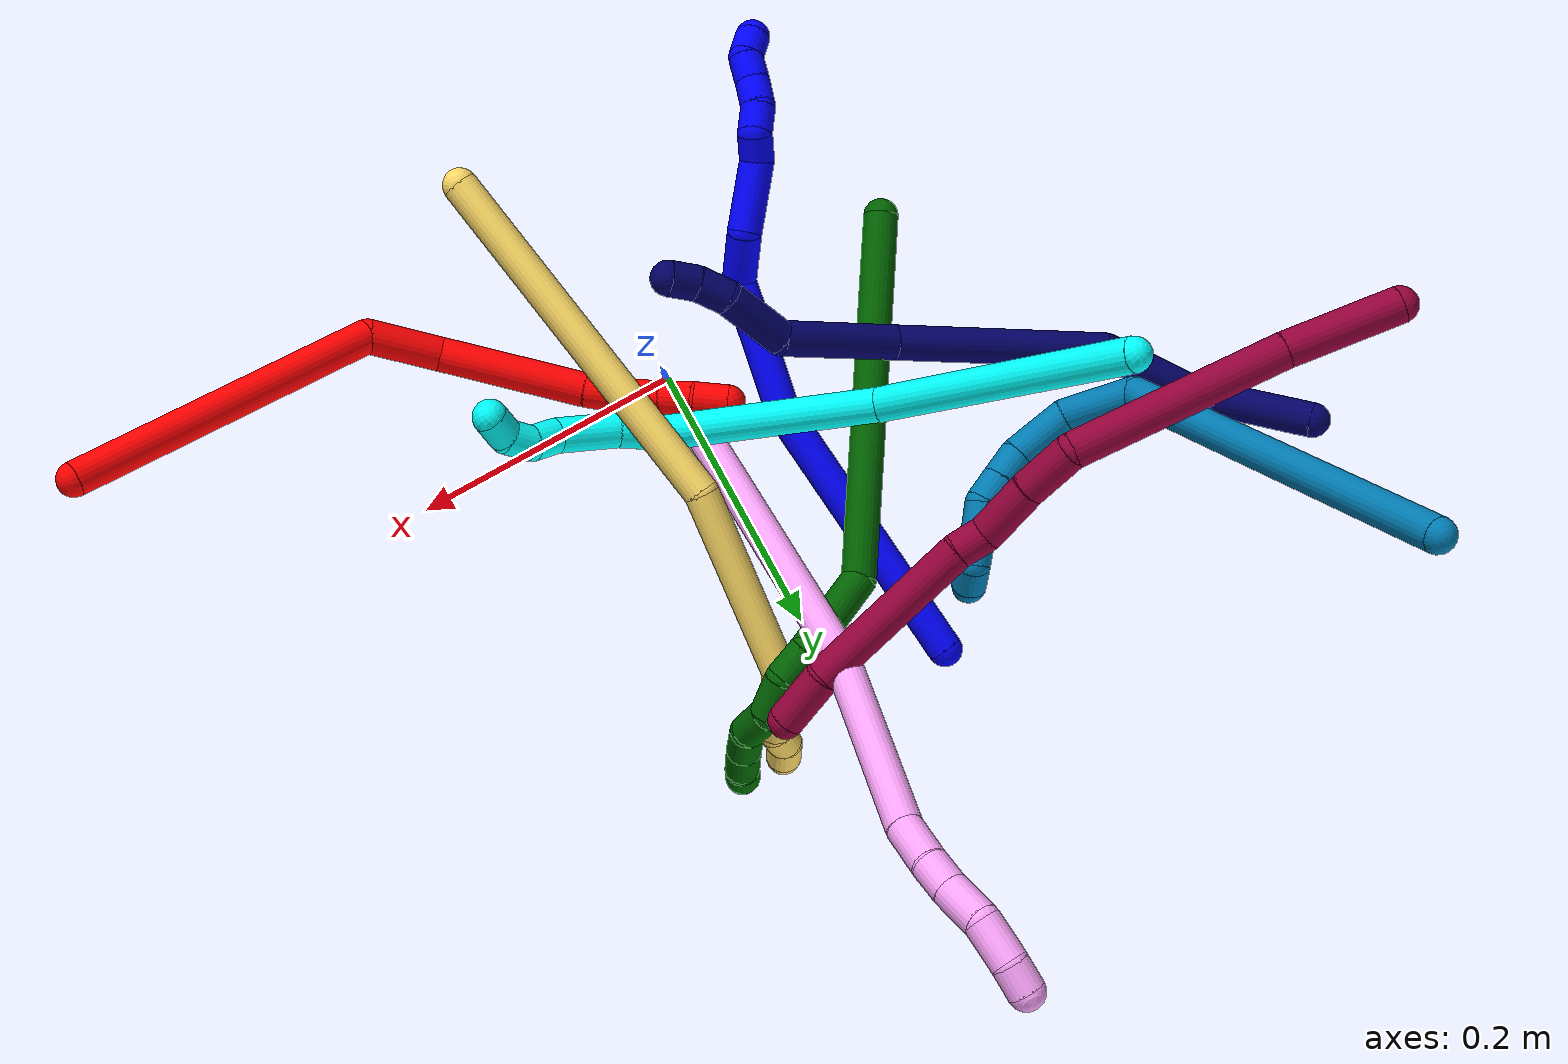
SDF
<sdf version="1.7">
 <world name="default">
  <plugin name="TubeGeneratorPlugin" filename="libtube_generator_plugin.so"/>
  <model name="photoneo_s_sensor">
   <static>1</static>
   <pose>0 0 2 1.57079 1.57079 3.14159</pose>
   <link name="link">
    <inertial><mass>0.1</mass></inertial>
    <sensor name="sensor" type="depth">
     <update_rate>30</update_rate>
     <camera>
      <horizontal_fov>1.22</horizontal_fov>
      <image><width>1920</width><height>1200</height><format>B8G8R8</format></image>
      <clip><near>0.1</near><far>4</far></clip>
      <depth_camera><output>points</output></depth_camera>
     </camera>
     <plugin name="camera_plugin" filename="libgazebo_ros_depth_camera.so">
      <baseline>0.2</baseline>
      <alwaysOn>1</alwaysOn>
      <updateRate>0.0</updateRate>
      <cameraName>camera_ir</cameraName>
      <imageTopicName>/camera/color/image_raw</imageTopicName>
      <cameraInfoTopicName>/camera/color/camera_info</cameraInfoTopicName>
      <depthImageTopicName>/camera/depth/image_raw</depthImageTopicName>
      <depthImageCameraInfoTopicName>/camera/depth/camera_info</depthImageCameraInfoTopicName>
      <pointCloudTopicName>/camera/depth/points</pointCloudTopicName>
      <frameName>fr_optical</frameName>
      <pointCloudCutoff>0.1</pointCloudCutoff>
      <pointCloudCutoffMax>2.0</pointCloudCutoffMax>
      <distortionK1>0</distortionK1>
      <distortionK2>0</distortionK2>
      <distortionK3>0</distortionK3>
      <distortionT1>0</distortionT1>
      <distortionT2>0</distortionT2>
      <CxPrime>0</CxPrime>
      <Cx>0</Cx>
      <Cy>0</Cy>
      <focalLength>0</focalLength>
      <hackBaseline>0</hackBaseline>
     </plugin>
    </sensor>
   </link>
  </model>
  <gravity>0 0 -9.8</gravity>
  <magnetic_field>6e-06 2.3e-05 -4.2e-05</magnetic_field>
  <atmosphere type="adiabatic"/>
  <physics name="default_physics" default="0" type="ode">
   <max_step_size>0.003</max_step_size>
   <real_time_factor>1</real_time_factor>
   <real_time_update_rate>1000</real_time_update_rate>
   <max_contacts>10000</max_contacts>
   <ode>
    <solver>
     <type>quick</type>
     <iters>100</iters>
     <sor>1.3</sor>
     <use_dynamic_moi_rescaling>0</use_dynamic_moi_rescaling>
    </solver>
    <constraints>
     <contact_max_correcting_vel>0</contact_max_correcting_vel>
     <contact_surface_layer>0.001</contact_surface_layer>
     <cfm>0</cfm>
     <erp>0.2</erp>
    </constraints>
   </ode>
  </physics>
  <scene><ambient>0.4 0.4 0.4 1</ambient><background>0.7 0.7 0.7 1</background><shadows>0</shadows></scene>
  <audio><device>default</device></audio>
  <spherical_coordinates>
   <surface_model>EARTH_WGS84</surface_model>
   <latitude_deg>0</latitude_deg>
   <longitude_deg>0</longitude_deg>
   <elevation>0</elevation>
   <heading_deg>0</heading_deg>
  </spherical_coordinates>
  <model name="bin">
   <static>1</static>
   <link name="bottom">
    <collision name="collision-bottom">
     <pose>0 0 -0.01 0 -0 0</pose>
     <geometry><box><size>0.8 0.6 0.02</size></box></geometry>
     <surface>
      <friction><ode><mu>100</mu><mu2>100</mu2></ode></friction>
      <contact><collide_bitmask>65535</collide_bitmask></contact>
     </surface>
    </collision>
   </link>
   <link name="west_wall">
    <collision name="collision-west_wall">
     <pose>-0.41 0 0.1 0 -0 0</pose>
     <geometry><box><size>0.02 0.6 0.2</size></box></geometry>
     <surface>
      <friction><ode><mu>100</mu><mu2>100</mu2></ode></friction>
      <contact><collide_bitmask>65535</collide_bitmask></contact>
     </surface>
    </collision>
   </link>
   <link name="east_wall">
    <collision name="collision-east_wall">
     <pose>0.41 0 0.1 0 -0 0</pose>
     <geometry><box><size>0.02 0.6 0.2</size></box></geometry>
     <surface>
      <friction><ode><mu>100</mu><mu2>100</mu2></ode></friction>
      <contact><collide_bitmask>65535</collide_bitmask></contact>
     </surface>
    </collision>
   </link>
   <link name="south_wall">
    <collision name="collision-south_wall">
     <pose>0 -0.31 0.1 0 -0 0</pose>
     <geometry><box><size>0.8 0.02 0.2</size></box></geometry>
     <surface>
      <friction><ode><mu>100</mu><mu2>100</mu2></ode></friction>
      <contact><collide_bitmask>65535</collide_bitmask></contact>
     </surface>
    </collision>
   </link>
   <link name="north_wall">
    <collision name="collision-north_wall">
     <pose>0 0.31 0.1 0 -0 0</pose>
     <geometry><box><size>0.8 0.02 0.2</size></box></geometry>
     <surface>
      <friction><ode><mu>100</mu><mu2>100</mu2></ode></friction>
      <contact><collide_bitmask>65535</collide_bitmask></contact>
     </surface>
    </collision>
   </link>
  </model>
  <model name="1">
   <static>0</static>
   <link name="1">
    <collision name="collision-cylinder-e_1_1_4">
     <pose>0.017731 -0.095347 0.035401 1.21529 0.172601 0.120183</pose>
     <geometry><cylinder><radius>0.0125</radius><length>0.206483</length></cylinder></geometry>
     <surface>
      <friction><ode><mu>1.16</mu><mu2>1.16</mu2><slip1>0</slip1><slip2>0</slip2></ode></friction>
      <contact><ode><kp>1e+06</kp><kd>1</kd><max_vel>0</max_vel><min_depth>0.001</min_depth></ode></contact>
     </surface>
    </collision>
    <visual name="visual-cylinder-e_1_1_4">
     <pose>0.017731 -0.095347 0.035401 1.21529 0.172601 0.120183</pose>
     <geometry><cylinder><radius>0.0125</radius><length>0.206483</length></cylinder></geometry>
     <material><ambient>0 0 1 1</ambient></material>
    </visual>
    <collision name="collision-cylinder-e_2_4_5">
     <pose>0.031069 -0.235644 0.091899 1.13198 -0.088247 -0.056088</pose>
     <geometry><cylinder><radius>0.0125</radius><length>0.099696</length></cylinder></geometry>
     <surface>
      <friction><ode><mu>1.16</mu><mu2>1.16</mu2><slip1>0</slip1><slip2>0</slip2></ode></friction>
      <contact><ode><kp>1e+06</kp><kd>1</kd><max_vel>0</max_vel><min_depth>0.001</min_depth></ode></contact>
     </surface>
    </collision>
    <visual name="visual-cylinder-e_2_4_5">
     <pose>0.031069 -0.235644 0.091899 1.13198 -0.088247 -0.056088</pose>
     <geometry><cylinder><radius>0.0125</radius><length>0.099696</length></cylinder></geometry>
     <material><ambient>0 0 1 1</ambient></material>
    </visual>
    <collision name="collision-cylinder-e_3_5_6">
     <pose>0.022548 -0.288642 0.13057 0.429436 -0.210375 -0.04604</pose>
     <geometry><cylinder><radius>0.0125</radius><length>0.039532</length></cylinder></geometry>
     <surface>
      <friction><ode><mu>1.16</mu><mu2>1.16</mu2><slip1>0</slip1><slip2>0</slip2></ode></friction>
      <contact><ode><kp>1e+06</kp><kd>1</kd><max_vel>0</max_vel><min_depth>0.001</min_depth></ode></contact>
     </surface>
    </collision>
    <visual name="visual-cylinder-e_3_5_6">
     <pose>0.022548 -0.288642 0.13057 0.429436 -0.210375 -0.04604</pose>
     <geometry><cylinder><radius>0.0125</radius><length>0.039532</length></cylinder></geometry>
     <material><ambient>0 0 1 1</ambient></material>
    </visual>
    <collision name="collision-cylinder-e_4_6_7">
     <pose>0.005068 -0.314291 0.162009 0.90361 -0.53746 -0.265711</pose>
     <geometry><cylinder><radius>0.0125</radius><length>0.052163</length></cylinder></geometry>
     <surface>
      <friction><ode><mu>1.16</mu><mu2>1.16</mu2><slip1>0</slip1><slip2>0</slip2></ode></friction>
      <contact><ode><kp>1e+06</kp><kd>1</kd><max_vel>0</max_vel><min_depth>0.001</min_depth></ode></contact>
     </surface>
    </collision>
    <visual name="visual-cylinder-e_4_6_7">
     <pose>0.005068 -0.314291 0.162009 0.90361 -0.53746 -0.265711</pose>
     <geometry><cylinder><radius>0.0125</radius><length>0.052163</length></cylinder></geometry>
     <material><ambient>0 0 1 1</ambient></material>
    </visual>
    <collision name="collision-cylinder-e_5_7_8">
     <pose>-0.009372 -0.337609 0.184198 0.601823 -0.107201 -0.033297</pose>
     <geometry><cylinder><radius>0.0125</radius><length>0.020318</length></cylinder></geometry>
     <surface>
      <friction><ode><mu>1.16</mu><mu2>1.16</mu2><slip1>0</slip1><slip2>0</slip2></ode></friction>
      <contact><ode><kp>1e+06</kp><kd>1</kd><max_vel>0</max_vel><min_depth>0.001</min_depth></ode></contact>
     </surface>
    </collision>
    <visual name="visual-cylinder-e_5_7_8">
     <pose>-0.009372 -0.337609 0.184198 0.601823 -0.107201 -0.033297</pose>
     <geometry><cylinder><radius>0.0125</radius><length>0.020318</length></cylinder></geometry>
     <material><ambient>0 0 1 1</ambient></material>
    </visual>
    <collision name="collision-cylinder-e_6_8_9">
     <pose>-0.01613 -0.351374 0.195424 1.22494 -0.585535 -0.417401</pose>
     <geometry><cylinder><radius>0.0125</radius><length>0.020524</length></cylinder></geometry>
     <surface>
      <friction><ode><mu>1.16</mu><mu2>1.16</mu2><slip1>0</slip1><slip2>0</slip2></ode></friction>
      <contact><ode><kp>1e+06</kp><kd>1</kd><max_vel>0</max_vel><min_depth>0.001</min_depth></ode></contact>
     </surface>
    </collision>
    <visual name="visual-cylinder-e_6_8_9">
     <pose>-0.01613 -0.351374 0.195424 1.22494 -0.585535 -0.417401</pose>
     <geometry><cylinder><radius>0.0125</radius><length>0.020524</length></cylinder></geometry>
     <material><ambient>0 0 1 1</ambient></material>
    </visual>
    <collision name="collision-cylinder-e_7_9_10">
     <pose>-0.025073 -0.368917 0.199347 1.46337 -0.330038 -0.29688</pose>
     <geometry><cylinder><radius>0.0125</radius><length>0.020192</length></cylinder></geometry>
     <surface>
      <friction><ode><mu>1.16</mu><mu2>1.16</mu2><slip1>0</slip1><slip2>0</slip2></ode></friction>
      <contact><ode><kp>1e+06</kp><kd>1</kd><max_vel>0</max_vel><min_depth>0.001</min_depth></ode></contact>
     </surface>
    </collision>
    <visual name="visual-cylinder-e_7_9_10">
     <pose>-0.025073 -0.368917 0.199347 1.46337 -0.330038 -0.29688</pose>
     <geometry><cylinder><radius>0.0125</radius><length>0.020192</length></cylinder></geometry>
     <material><ambient>0 0 1 1</ambient></material>
    </visual>
    <collision name="collision-cylinder-e_8_10_11">
     <pose>-0.030863 -0.388068 0.202064 1.39728 -0.251373 -0.211472</pose>
     <geometry><cylinder><radius>0.0125</radius><length>0.020241</length></cylinder></geometry>
     <surface>
      <friction><ode><mu>1.16</mu><mu2>1.16</mu2><slip1>0</slip1><slip2>0</slip2></ode></friction>
      <contact><ode><kp>1e+06</kp><kd>1</kd><max_vel>0</max_vel><min_depth>0.001</min_depth></ode></contact>
     </surface>
    </collision>
    <visual name="visual-cylinder-e_8_10_11">
     <pose>-0.030863 -0.388068 0.202064 1.39728 -0.251373 -0.211472</pose>
     <geometry><cylinder><radius>0.0125</radius><length>0.020241</length></cylinder></geometry>
     <material><ambient>0 0 1 1</ambient></material>
    </visual>
    <collision name="collision-cylinder-e_9_11_2">
     <pose>-0.040684 -0.405158 0.203509 1.60405 -0.776213 -0.799793</pose>
     <geometry><cylinder><radius>0.0125</radius><length>0.02085</length></cylinder></geometry>
     <surface>
      <friction><ode><mu>1.16</mu><mu2>1.16</mu2><slip1>0</slip1><slip2>0</slip2></ode></friction>
      <contact><ode><kp>1e+06</kp><kd>1</kd><max_vel>0</max_vel><min_depth>0.001</min_depth></ode></contact>
     </surface>
    </collision>
    <visual name="visual-cylinder-e_9_11_2">
     <pose>-0.040684 -0.405158 0.203509 1.60405 -0.776213 -0.799793</pose>
     <geometry><cylinder><radius>0.0125</radius><length>0.02085</length></cylinder></geometry>
     <material><ambient>0 0 1 1</ambient></material>
    </visual>
    <collision name="collision-sphere-2">
     <pose>-0.047987 -0.412593 0.203261 0 -0 0</pose>
     <geometry><sphere><radius>0.0125</radius></sphere></geometry>
     <surface>
      <friction><ode><mu>1.16</mu><mu2>1.16</mu2><slip1>0</slip1><slip2>0</slip2></ode></friction>
      <contact><ode><kp>1e+06</kp><kd>1</kd><max_vel>0</max_vel><min_depth>0.001</min_depth></ode></contact>
     </surface>
    </collision>
    <visual name="visual-sphere-2">
     <pose>-0.047987 -0.412593 0.203261 0 -0 0</pose>
     <geometry><sphere><radius>0.0125</radius></sphere></geometry>
     <material><ambient>0 0 1 1</ambient></material>
    </visual>
    <collision name="collision-sphere-11">
     <pose>-0.03338 -0.397724 0.203756 0 -0 0</pose>
     <geometry><sphere><radius>0.0125</radius></sphere></geometry>
     <surface>
      <friction><ode><mu>1.16</mu><mu2>1.16</mu2><slip1>0</slip1><slip2>0</slip2></ode></friction>
      <contact><ode><kp>1e+06</kp><kd>1</kd><max_vel>0</max_vel><min_depth>0.001</min_depth></ode></contact>
     </surface>
    </collision>
    <visual name="visual-sphere-11">
     <pose>-0.03338 -0.397724 0.203756 0 -0 0</pose>
     <geometry><sphere><radius>0.0125</radius></sphere></geometry>
     <material><ambient>0 0 1 1</ambient></material>
    </visual>
    <collision name="collision-sphere-10">
     <pose>-0.028345 -0.378413 0.200371 0 -0 0</pose>
     <geometry><sphere><radius>0.0125</radius></sphere></geometry>
     <surface>
      <friction><ode><mu>1.16</mu><mu2>1.16</mu2><slip1>0</slip1><slip2>0</slip2></ode></friction>
      <contact><ode><kp>1e+06</kp><kd>1</kd><max_vel>0</max_vel><min_depth>0.001</min_depth></ode></contact>
     </surface>
    </collision>
    <visual name="visual-sphere-10">
     <pose>-0.028345 -0.378413 0.200371 0 -0 0</pose>
     <geometry><sphere><radius>0.0125</radius></sphere></geometry>
     <material><ambient>0 0 1 1</ambient></material>
    </visual>
    <collision name="collision-sphere-9">
     <pose>-0.021801 -0.35942 0.198323 0 -0 0</pose>
     <geometry><sphere><radius>0.0125</radius></sphere></geometry>
     <surface>
      <friction><ode><mu>1.16</mu><mu2>1.16</mu2><slip1>0</slip1><slip2>0</slip2></ode></friction>
      <contact><ode><kp>1e+06</kp><kd>1</kd><max_vel>0</max_vel><min_depth>0.001</min_depth></ode></contact>
     </surface>
    </collision>
    <visual name="visual-sphere-9">
     <pose>-0.021801 -0.35942 0.198323 0 -0 0</pose>
     <geometry><sphere><radius>0.0125</radius></sphere></geometry>
     <material><ambient>0 0 1 1</ambient></material>
    </visual>
    <collision name="collision-sphere-4">
     <pose>0.035462 -0.190695 0.070802 0 -0 0</pose>
     <geometry><sphere><radius>0.0125</radius></sphere></geometry>
     <surface>
      <friction><ode><mu>1.16</mu><mu2>1.16</mu2><slip1>0</slip1><slip2>0</slip2></ode></friction>
      <contact><ode><kp>1e+06</kp><kd>1</kd><max_vel>0</max_vel><min_depth>0.001</min_depth></ode></contact>
     </surface>
    </collision>
    <visual name="visual-sphere-4">
     <pose>0.035462 -0.190695 0.070802 0 -0 0</pose>
     <geometry><sphere><radius>0.0125</radius></sphere></geometry>
     <material><ambient>0 0 1 1</ambient></material>
    </visual>
    <collision name="collision-sphere-1">
     <geometry><sphere><radius>0.0125</radius></sphere></geometry>
     <surface>
      <friction><ode><mu>1.16</mu><mu2>1.16</mu2><slip1>0</slip1><slip2>0</slip2></ode></friction>
      <contact><ode><kp>1e+06</kp><kd>1</kd><max_vel>0</max_vel><min_depth>0.001</min_depth></ode></contact>
     </surface>
    </collision>
    <visual name="visual-sphere-1">
     <geometry><sphere><radius>0.0125</radius></sphere></geometry>
     <material><ambient>0 0 1 1</ambient></material>
    </visual>
    <collision name="collision-sphere-8">
     <pose>-0.010459 -0.343328 0.192524 0 -0 0</pose>
     <geometry><sphere><radius>0.0125</radius></sphere></geometry>
     <surface>
      <friction><ode><mu>1.16</mu><mu2>1.16</mu2><slip1>0</slip1><slip2>0</slip2></ode></friction>
      <contact><ode><kp>1e+06</kp><kd>1</kd><max_vel>0</max_vel><min_depth>0.001</min_depth></ode></contact>
     </surface>
    </collision>
    <visual name="visual-sphere-8">
     <pose>-0.010459 -0.343328 0.192524 0 -0 0</pose>
     <geometry><sphere><radius>0.0125</radius></sphere></geometry>
     <material><ambient>0 0 1 1</ambient></material>
    </visual>
    <collision name="collision-sphere-5">
     <pose>0.026676 -0.280594 0.112995 0 -0 0</pose>
     <geometry><sphere><radius>0.0125</radius></sphere></geometry>
     <surface>
      <friction><ode><mu>1.16</mu><mu2>1.16</mu2><slip1>0</slip1><slip2>0</slip2></ode></friction>
      <contact><ode><kp>1e+06</kp><kd>1</kd><max_vel>0</max_vel><min_depth>0.001</min_depth></ode></contact>
     </surface>
    </collision>
    <visual name="visual-sphere-5">
     <pose>0.026676 -0.280594 0.112995 0 -0 0</pose>
     <geometry><sphere><radius>0.0125</radius></sphere></geometry>
     <material><ambient>0 0 1 1</ambient></material>
    </visual>
    <collision name="collision-sphere-6">
     <pose>0.01842 -0.296691 0.148145 0 -0 0</pose>
     <geometry><sphere><radius>0.0125</radius></sphere></geometry>
     <surface>
      <friction><ode><mu>1.16</mu><mu2>1.16</mu2><slip1>0</slip1><slip2>0</slip2></ode></friction>
      <contact><ode><kp>1e+06</kp><kd>1</kd><max_vel>0</max_vel><min_depth>0.001</min_depth></ode></contact>
     </surface>
    </collision>
    <visual name="visual-sphere-6">
     <pose>0.01842 -0.296691 0.148145 0 -0 0</pose>
     <geometry><sphere><radius>0.0125</radius></sphere></geometry>
     <material><ambient>0 0 1 1</ambient></material>
    </visual>
    <collision name="collision-sphere-7">
     <pose>-0.008285 -0.331891 0.175872 0 -0 0</pose>
     <geometry><sphere><radius>0.0125</radius></sphere></geometry>
     <surface>
      <friction><ode><mu>1.16</mu><mu2>1.16</mu2><slip1>0</slip1><slip2>0</slip2></ode></friction>
      <contact><ode><kp>1e+06</kp><kd>1</kd><max_vel>0</max_vel><min_depth>0.001</min_depth></ode></contact>
     </surface>
    </collision>
    <visual name="visual-sphere-7">
     <pose>-0.008285 -0.331891 0.175872 0 -0 0</pose>
     <geometry><sphere><radius>0.0125</radius></sphere></geometry>
     <material><ambient>0 0 1 1</ambient></material>
    </visual>
    <inertial>
     <pose>0.010827 -0.217617 0.100392 0 -0 0</pose>
     <mass>0.5</mass>
     <inertia>
      <ixx>0.000909</ixx>
      <ixy>0</ixy>
      <ixz>0</ixz>
      <iyy>0.000372</iyy>
      <iyz>0</iyz>
      <izz>0.000689</izz>
     </inertia>
    </inertial>
   </link>
   <pose>-0.081181 0.267529 0.011889 0.417414 -0.36829 -0.084925</pose>
  </model>
  <model name="2">
   <static>0</static>
   <link name="2">
    <collision name="collision-cylinder-e_1_1_4">
     <pose>-0.025797 -0.002825 -0.1136 3.11673 -0.223234 -2.92069</pose>
     <geometry><cylinder><radius>0.0125</radius><length>0.233054</length></cylinder></geometry>
     <surface>
      <friction><ode><mu>1.16</mu><mu2>1.16</mu2><slip1>0</slip1><slip2>0</slip2></ode></friction>
      <contact><ode><kp>1e+06</kp><kd>1</kd><max_vel>0</max_vel><min_depth>0.001</min_depth></ode></contact>
     </surface>
    </collision>
    <visual name="visual-cylinder-e_1_1_4">
     <pose>-0.025797 -0.002825 -0.1136 3.11673 -0.223234 -2.92069</pose>
     <geometry><cylinder><radius>0.0125</radius><length>0.233054</length></cylinder></geometry>
     <material><ambient>1 0 0 1</ambient></material>
    </visual>
    <collision name="collision-cylinder-e_2_4_5">
     <pose>-0.05864 0.011151 -0.247367 -2.44698 -0.262236 0.698746</pose>
     <geometry><cylinder><radius>0.0125</radius><length>0.054353</length></cylinder></geometry>
     <surface>
      <friction><ode><mu>1.16</mu><mu2>1.16</mu2><slip1>0</slip1><slip2>0</slip2></ode></friction>
      <contact><ode><kp>1e+06</kp><kd>1</kd><max_vel>0</max_vel><min_depth>0.001</min_depth></ode></contact>
     </surface>
    </collision>
    <visual name="visual-cylinder-e_2_4_5">
     <pose>-0.05864 0.011151 -0.247367 -2.44698 -0.262236 0.698746</pose>
     <geometry><cylinder><radius>0.0125</radius><length>0.054353</length></cylinder></geometry>
     <material><ambient>1 0 0 1</ambient></material>
    </visual>
    <collision name="collision-cylinder-e_3_5_6">
     <pose>-0.095772 0.061675 -0.297308 -2.2941 -0.58948 1.18478</pose>
     <geometry><cylinder><radius>0.0125</radius><length>0.10824</length></cylinder></geometry>
     <surface>
      <friction><ode><mu>1.16</mu><mu2>1.16</mu2><slip1>0</slip1><slip2>0</slip2></ode></friction>
      <contact><ode><kp>1e+06</kp><kd>1</kd><max_vel>0</max_vel><min_depth>0.001</min_depth></ode></contact>
     </surface>
    </collision>
    <visual name="visual-cylinder-e_3_5_6">
     <pose>-0.095772 0.061675 -0.297308 -2.2941 -0.58948 1.18478</pose>
     <geometry><cylinder><radius>0.0125</radius><length>0.10824</length></cylinder></geometry>
     <material><ambient>1 0 0 1</ambient></material>
    </visual>
    <collision name="collision-cylinder-e_4_6_7">
     <pose>-0.133694 0.10203 -0.333666 -2.35244 -0.697731 1.43597</pose>
     <geometry><cylinder><radius>0.0125</radius><length>0.024391</length></cylinder></geometry>
     <surface>
      <friction><ode><mu>1.16</mu><mu2>1.16</mu2><slip1>0</slip1><slip2>0</slip2></ode></friction>
      <contact><ode><kp>1e+06</kp><kd>1</kd><max_vel>0</max_vel><min_depth>0.001</min_depth></ode></contact>
     </surface>
    </collision>
    <visual name="visual-cylinder-e_4_6_7">
     <pose>-0.133694 0.10203 -0.333666 -2.35244 -0.697731 1.43597</pose>
     <geometry><cylinder><radius>0.0125</radius><length>0.024391</length></cylinder></geometry>
     <material><ambient>1 0 0 1</ambient></material>
    </visual>
    <collision name="collision-cylinder-e_5_7_8">
     <pose>-0.15235 0.115889 -0.348442 -2.41887 -0.78063 1.65554</pose>
     <geometry><cylinder><radius>0.0125</radius><length>0.030751</length></cylinder></geometry>
     <surface>
      <friction><ode><mu>1.16</mu><mu2>1.16</mu2><slip1>0</slip1><slip2>0</slip2></ode></friction>
      <contact><ode><kp>1e+06</kp><kd>1</kd><max_vel>0</max_vel><min_depth>0.001</min_depth></ode></contact>
     </surface>
    </collision>
    <visual name="visual-cylinder-e_5_7_8">
     <pose>-0.15235 0.115889 -0.348442 -2.41887 -0.78063 1.65554</pose>
     <geometry><cylinder><radius>0.0125</radius><length>0.030751</length></cylinder></geometry>
     <material><ambient>1 0 0 1</ambient></material>
    </visual>
    <collision name="collision-cylinder-e_6_8_9">
     <pose>-0.17227 0.128184 -0.362941 -2.46439 -0.844065 1.8114</pose>
     <geometry><cylinder><radius>0.0125</radius><length>0.024354</length></cylinder></geometry>
     <surface>
      <friction><ode><mu>1.16</mu><mu2>1.16</mu2><slip1>0</slip1><slip2>0</slip2></ode></friction>
      <contact><ode><kp>1e+06</kp><kd>1</kd><max_vel>0</max_vel><min_depth>0.001</min_depth></ode></contact>
     </surface>
    </collision>
    <visual name="visual-cylinder-e_6_8_9">
     <pose>-0.17227 0.128184 -0.362941 -2.46439 -0.844065 1.8114</pose>
     <geometry><cylinder><radius>0.0125</radius><length>0.024354</length></cylinder></geometry>
     <material><ambient>1 0 0 1</ambient></material>
    </visual>
    <collision name="collision-cylinder-e_7_9_2">
     <pose>-0.189029 0.139491 -0.37679 -2.45068 -0.663877 1.52766</pose>
     <geometry><cylinder><radius>0.0125</radius><length>0.024857</length></cylinder></geometry>
     <surface>
      <friction><ode><mu>1.16</mu><mu2>1.16</mu2><slip1>0</slip1><slip2>0</slip2></ode></friction>
      <contact><ode><kp>1e+06</kp><kd>1</kd><max_vel>0</max_vel><min_depth>0.001</min_depth></ode></contact>
     </surface>
    </collision>
    <visual name="visual-cylinder-e_7_9_2">
     <pose>-0.189029 0.139491 -0.37679 -2.45068 -0.663877 1.52766</pose>
     <geometry><cylinder><radius>0.0125</radius><length>0.024857</length></cylinder></geometry>
     <material><ambient>1 0 0 1</ambient></material>
    </visual>
    <collision name="collision-sphere-2">
     <pose>-0.196687 0.145729 -0.384334 0 -0 0</pose>
     <geometry><sphere><radius>0.0125</radius></sphere></geometry>
     <surface>
      <friction><ode><mu>1.16</mu><mu2>1.16</mu2><slip1>0</slip1><slip2>0</slip2></ode></friction>
      <contact><ode><kp>1e+06</kp><kd>1</kd><max_vel>0</max_vel><min_depth>0.001</min_depth></ode></contact>
     </surface>
    </collision>
    <visual name="visual-sphere-2">
     <pose>-0.196687 0.145729 -0.384334 0 -0 0</pose>
     <geometry><sphere><radius>0.0125</radius></sphere></geometry>
     <material><ambient>1 0 0 1</ambient></material>
    </visual>
    <collision name="collision-sphere-9">
     <pose>-0.181371 0.133253 -0.369246 0 -0 0</pose>
     <geometry><sphere><radius>0.0125</radius></sphere></geometry>
     <surface>
      <friction><ode><mu>1.16</mu><mu2>1.16</mu2><slip1>0</slip1><slip2>0</slip2></ode></friction>
      <contact><ode><kp>1e+06</kp><kd>1</kd><max_vel>0</max_vel><min_depth>0.001</min_depth></ode></contact>
     </surface>
    </collision>
    <visual name="visual-sphere-9">
     <pose>-0.181371 0.133253 -0.369246 0 -0 0</pose>
     <geometry><sphere><radius>0.0125</radius></sphere></geometry>
     <material><ambient>1 0 0 1</ambient></material>
    </visual>
    <collision name="collision-sphere-4">
     <pose>-0.051594 -0.005649 -0.227201 0 -0 0</pose>
     <geometry><sphere><radius>0.0125</radius></sphere></geometry>
     <surface>
      <friction><ode><mu>1.16</mu><mu2>1.16</mu2><slip1>0</slip1><slip2>0</slip2></ode></friction>
      <contact><ode><kp>1e+06</kp><kd>1</kd><max_vel>0</max_vel><min_depth>0.001</min_depth></ode></contact>
     </surface>
    </collision>
    <visual name="visual-sphere-4">
     <pose>-0.051594 -0.005649 -0.227201 0 -0 0</pose>
     <geometry><sphere><radius>0.0125</radius></sphere></geometry>
     <material><ambient>1 0 0 1</ambient></material>
    </visual>
    <collision name="collision-sphere-1">
     <geometry><sphere><radius>0.0125</radius></sphere></geometry>
     <surface>
      <friction><ode><mu>1.16</mu><mu2>1.16</mu2><slip1>0</slip1><slip2>0</slip2></ode></friction>
      <contact><ode><kp>1e+06</kp><kd>1</kd><max_vel>0</max_vel><min_depth>0.001</min_depth></ode></contact>
     </surface>
    </collision>
    <visual name="visual-sphere-1">
     <geometry><sphere><radius>0.0125</radius></sphere></geometry>
     <material><ambient>1 0 0 1</ambient></material>
    </visual>
    <collision name="collision-sphere-8">
     <pose>-0.16317 0.123114 -0.356635 0 -0 0</pose>
     <geometry><sphere><radius>0.0125</radius></sphere></geometry>
     <surface>
      <friction><ode><mu>1.16</mu><mu2>1.16</mu2><slip1>0</slip1><slip2>0</slip2></ode></friction>
      <contact><ode><kp>1e+06</kp><kd>1</kd><max_vel>0</max_vel><min_depth>0.001</min_depth></ode></contact>
     </surface>
    </collision>
    <visual name="visual-sphere-8">
     <pose>-0.16317 0.123114 -0.356635 0 -0 0</pose>
     <geometry><sphere><radius>0.0125</radius></sphere></geometry>
     <material><ambient>1 0 0 1</ambient></material>
    </visual>
    <collision name="collision-sphere-5">
     <pose>-0.065685 0.027952 -0.267533 0 -0 0</pose>
     <geometry><sphere><radius>0.0125</radius></sphere></geometry>
     <surface>
      <friction><ode><mu>1.16</mu><mu2>1.16</mu2><slip1>0</slip1><slip2>0</slip2></ode></friction>
      <contact><ode><kp>1e+06</kp><kd>1</kd><max_vel>0</max_vel><min_depth>0.001</min_depth></ode></contact>
     </surface>
    </collision>
    <visual name="visual-sphere-5">
     <pose>-0.065685 0.027952 -0.267533 0 -0 0</pose>
     <geometry><sphere><radius>0.0125</radius></sphere></geometry>
     <material><ambient>1 0 0 1</ambient></material>
    </visual>
    <collision name="collision-sphere-6">
     <pose>-0.125859 0.095397 -0.327083 0 -0 0</pose>
     <geometry><sphere><radius>0.0125</radius></sphere></geometry>
     <surface>
      <friction><ode><mu>1.16</mu><mu2>1.16</mu2><slip1>0</slip1><slip2>0</slip2></ode></friction>
      <contact><ode><kp>1e+06</kp><kd>1</kd><max_vel>0</max_vel><min_depth>0.001</min_depth></ode></contact>
     </surface>
    </collision>
    <visual name="visual-sphere-6">
     <pose>-0.125859 0.095397 -0.327083 0 -0 0</pose>
     <geometry><sphere><radius>0.0125</radius></sphere></geometry>
     <material><ambient>1 0 0 1</ambient></material>
    </visual>
    <collision name="collision-sphere-7">
     <pose>-0.141529 0.108663 -0.340249 0 -0 0</pose>
     <geometry><sphere><radius>0.0125</radius></sphere></geometry>
     <surface>
      <friction><ode><mu>1.16</mu><mu2>1.16</mu2><slip1>0</slip1><slip2>0</slip2></ode></friction>
      <contact><ode><kp>1e+06</kp><kd>1</kd><max_vel>0</max_vel><min_depth>0.001</min_depth></ode></contact>
     </surface>
    </collision>
    <visual name="visual-sphere-7">
     <pose>-0.141529 0.108663 -0.340249 0 -0 0</pose>
     <geometry><sphere><radius>0.0125</radius></sphere></geometry>
     <material><ambient>1 0 0 1</ambient></material>
    </visual>
    <inertial>
     <pose>-0.072811 0.03853 -0.218318 0 -0 0</pose>
     <mass>0.5</mass>
     <inertia>
      <ixx>-0.001108</ixx>
      <ixy>0</ixy>
      <ixz>0</ixz>
      <iyy>0.000937</iyy>
      <iyz>0</iyz>
      <izz>0.00022</izz>
     </inertia>
    </inertial>
   </link>
   <pose>0.384557 -0.127788 0.128634 -0.133982 0.898879 -0.167885</pose>
  </model>
  <model name="3">
   <static>0</static>
   <link name="3">
    <collision name="collision-cylinder-e_1_1_4">
     <pose>0.024106 0.023868 0.09809 -0.238688 0.2344 -0.028235</pose>
     <geometry><cylinder><radius>0.0125</radius><length>0.20758</length></cylinder></geometry>
     <surface>
      <friction><ode><mu>1.16</mu><mu2>1.16</mu2><slip1>0</slip1><slip2>0</slip2></ode></friction>
      <contact><ode><kp>1e+06</kp><kd>1</kd><max_vel>0</max_vel><min_depth>0.001</min_depth></ode></contact>
     </surface>
    </collision>
    <visual name="visual-cylinder-e_1_1_4">
     <pose>0.024106 0.023868 0.09809 -0.238688 0.2344 -0.028235</pose>
     <geometry><cylinder><radius>0.0125</radius><length>0.20758</length></cylinder></geometry>
     <material><ambient>0.003922 1 0.996078 1</ambient></material>
    </visual>
    <collision name="collision-cylinder-e_2_4_5">
     <pose>0.105239 0.052389 0.246114 -0.092914 0.849459 -0.042045</pose>
     <geometry><cylinder><radius>0.0125</radius><length>0.151883</length></cylinder></geometry>
     <surface>
      <friction><ode><mu>1.16</mu><mu2>1.16</mu2><slip1>0</slip1><slip2>0</slip2></ode></friction>
      <contact><ode><kp>1e+06</kp><kd>1</kd><max_vel>0</max_vel><min_depth>0.001</min_depth></ode></contact>
     </surface>
    </collision>
    <visual name="visual-cylinder-e_2_4_5">
     <pose>0.105239 0.052389 0.246114 -0.092914 0.849459 -0.042045</pose>
     <geometry><cylinder><radius>0.0125</radius><length>0.151883</length></cylinder></geometry>
     <material><ambient>0.003922 1 0.996078 1</ambient></material>
    </visual>
    <collision name="collision-cylinder-e_3_5_6">
     <pose>0.176905 0.059238 0.302499 -0.328184 1.13518 -0.210361</pose>
     <geometry><cylinder><radius>0.0125</radius><length>0.032296</length></cylinder></geometry>
     <surface>
      <friction><ode><mu>1.16</mu><mu2>1.16</mu2><slip1>0</slip1><slip2>0</slip2></ode></friction>
      <contact><ode><kp>1e+06</kp><kd>1</kd><max_vel>0</max_vel><min_depth>0.001</min_depth></ode></contact>
     </surface>
    </collision>
    <visual name="visual-cylinder-e_3_5_6">
     <pose>0.176905 0.059238 0.302499 -0.328184 1.13518 -0.210361</pose>
     <geometry><cylinder><radius>0.0125</radius><length>0.032296</length></cylinder></geometry>
     <material><ambient>0.003922 1 0.996078 1</ambient></material>
    </visual>
    <collision name="collision-cylinder-e_4_6_7">
     <pose>0.212443 0.060429 0.317089 0.122892 1.19685 0.083847</pose>
     <geometry><cylinder><radius>0.0125</radius><length>0.044899</length></cylinder></geometry>
     <surface>
      <friction><ode><mu>1.16</mu><mu2>1.16</mu2><slip1>0</slip1><slip2>0</slip2></ode></friction>
      <contact><ode><kp>1e+06</kp><kd>1</kd><max_vel>0</max_vel><min_depth>0.001</min_depth></ode></contact>
     </surface>
    </collision>
    <visual name="visual-cylinder-e_4_6_7">
     <pose>0.212443 0.060429 0.317089 0.122892 1.19685 0.083847</pose>
     <geometry><cylinder><radius>0.0125</radius><length>0.044899</length></cylinder></geometry>
     <material><ambient>0.003922 1 0.996078 1</ambient></material>
    </visual>
    <collision name="collision-cylinder-e_5_7_8">
     <pose>0.243834 0.055376 0.325927 1.3998 1.19763 1.04316</pose>
     <geometry><cylinder><radius>0.0125</radius><length>0.022537</length></cylinder></geometry>
     <surface>
      <friction><ode><mu>1.16</mu><mu2>1.16</mu2><slip1>0</slip1><slip2>0</slip2></ode></friction>
      <contact><ode><kp>1e+06</kp><kd>1</kd><max_vel>0</max_vel><min_depth>0.001</min_depth></ode></contact>
     </surface>
    </collision>
    <visual name="visual-cylinder-e_5_7_8">
     <pose>0.243834 0.055376 0.325927 1.3998 1.19763 1.04316</pose>
     <geometry><cylinder><radius>0.0125</radius><length>0.022537</length></cylinder></geometry>
     <material><ambient>0.003922 1 0.996078 1</ambient></material>
    </visual>
    <collision name="collision-cylinder-e_6_8_9">
     <pose>0.264399 0.052777 0.326421 -1.7109 1.42641 -1.56647</pose>
     <geometry><cylinder><radius>0.0125</radius><length>0.020355</length></cylinder></geometry>
     <surface>
      <friction><ode><mu>1.16</mu><mu2>1.16</mu2><slip1>0</slip1><slip2>0</slip2></ode></friction>
      <contact><ode><kp>1e+06</kp><kd>1</kd><max_vel>0</max_vel><min_depth>0.001</min_depth></ode></contact>
     </surface>
    </collision>
    <visual name="visual-cylinder-e_6_8_9">
     <pose>0.264399 0.052777 0.326421 -1.7109 1.42641 -1.56647</pose>
     <geometry><cylinder><radius>0.0125</radius><length>0.020355</length></cylinder></geometry>
     <material><ambient>0.003922 1 0.996078 1</ambient></material>
    </visual>
    <collision name="collision-cylinder-e_7_9_2">
     <pose>0.282674 0.058644 0.322006 -2.33223 0.931244 -1.72978</pose>
     <geometry><cylinder><radius>0.0125</radius><length>0.020449</length></cylinder></geometry>
     <surface>
      <friction><ode><mu>1.16</mu><mu2>1.16</mu2><slip1>0</slip1><slip2>0</slip2></ode></friction>
      <contact><ode><kp>1e+06</kp><kd>1</kd><max_vel>0</max_vel><min_depth>0.001</min_depth></ode></contact>
     </surface>
    </collision>
    <visual name="visual-cylinder-e_7_9_2">
     <pose>0.282674 0.058644 0.322006 -2.33223 0.931244 -1.72978</pose>
     <geometry><cylinder><radius>0.0125</radius><length>0.020449</length></cylinder></geometry>
     <material><ambient>0.003922 1 0.996078 1</ambient></material>
    </visual>
    <collision name="collision-sphere-2">
     <pose>0.290878 0.063062 0.317796 0 -0 0</pose>
     <geometry><sphere><radius>0.0125</radius></sphere></geometry>
     <surface>
      <friction><ode><mu>1.16</mu><mu2>1.16</mu2><slip1>0</slip1><slip2>0</slip2></ode></friction>
      <contact><ode><kp>1e+06</kp><kd>1</kd><max_vel>0</max_vel><min_depth>0.001</min_depth></ode></contact>
     </surface>
    </collision>
    <visual name="visual-sphere-2">
     <pose>0.290878 0.063062 0.317796 0 -0 0</pose>
     <geometry><sphere><radius>0.0125</radius></sphere></geometry>
     <material><ambient>0.003922 1 0.996078 1</ambient></material>
    </visual>
    <collision name="collision-sphere-9">
     <pose>0.274471 0.054227 0.326217 0 -0 0</pose>
     <geometry><sphere><radius>0.0125</radius></sphere></geometry>
     <surface>
      <friction><ode><mu>1.16</mu><mu2>1.16</mu2><slip1>0</slip1><slip2>0</slip2></ode></friction>
      <contact><ode><kp>1e+06</kp><kd>1</kd><max_vel>0</max_vel><min_depth>0.001</min_depth></ode></contact>
     </surface>
    </collision>
    <visual name="visual-sphere-9">
     <pose>0.274471 0.054227 0.326217 0 -0 0</pose>
     <geometry><sphere><radius>0.0125</radius></sphere></geometry>
     <material><ambient>0.003922 1 0.996078 1</ambient></material>
    </visual>
    <collision name="collision-sphere-4">
     <pose>0.048212 0.047736 0.19618 0 -0 0</pose>
     <geometry><sphere><radius>0.0125</radius></sphere></geometry>
     <surface>
      <friction><ode><mu>1.16</mu><mu2>1.16</mu2><slip1>0</slip1><slip2>0</slip2></ode></friction>
      <contact><ode><kp>1e+06</kp><kd>1</kd><max_vel>0</max_vel><min_depth>0.001</min_depth></ode></contact>
     </surface>
    </collision>
    <visual name="visual-sphere-4">
     <pose>0.048212 0.047736 0.19618 0 -0 0</pose>
     <geometry><sphere><radius>0.0125</radius></sphere></geometry>
     <material><ambient>0.003922 1 0.996078 1</ambient></material>
    </visual>
    <collision name="collision-sphere-1">
     <geometry><sphere><radius>0.0125</radius></sphere></geometry>
     <surface>
      <friction><ode><mu>1.16</mu><mu2>1.16</mu2><slip1>0</slip1><slip2>0</slip2></ode></friction>
      <contact><ode><kp>1e+06</kp><kd>1</kd><max_vel>0</max_vel><min_depth>0.001</min_depth></ode></contact>
     </surface>
    </collision>
    <visual name="visual-sphere-1">
     <geometry><sphere><radius>0.0125</radius></sphere></geometry>
     <material><ambient>0.003922 1 0.996078 1</ambient></material>
    </visual>
    <collision name="collision-sphere-8">
     <pose>0.254328 0.051327 0.326626 0 -0 0</pose>
     <geometry><sphere><radius>0.0125</radius></sphere></geometry>
     <surface>
      <friction><ode><mu>1.16</mu><mu2>1.16</mu2><slip1>0</slip1><slip2>0</slip2></ode></friction>
      <contact><ode><kp>1e+06</kp><kd>1</kd><max_vel>0</max_vel><min_depth>0.001</min_depth></ode></contact>
     </surface>
    </collision>
    <visual name="visual-sphere-8">
     <pose>0.254328 0.051327 0.326626 0 -0 0</pose>
     <geometry><sphere><radius>0.0125</radius></sphere></geometry>
     <material><ambient>0.003922 1 0.996078 1</ambient></material>
    </visual>
    <collision name="collision-sphere-5">
     <pose>0.162265 0.057042 0.296049 0 -0 0</pose>
     <geometry><sphere><radius>0.0125</radius></sphere></geometry>
     <surface>
      <friction><ode><mu>1.16</mu><mu2>1.16</mu2><slip1>0</slip1><slip2>0</slip2></ode></friction>
      <contact><ode><kp>1e+06</kp><kd>1</kd><max_vel>0</max_vel><min_depth>0.001</min_depth></ode></contact>
     </surface>
    </collision>
    <visual name="visual-sphere-5">
     <pose>0.162265 0.057042 0.296049 0 -0 0</pose>
     <geometry><sphere><radius>0.0125</radius></sphere></geometry>
     <material><ambient>0.003922 1 0.996078 1</ambient></material>
    </visual>
    <collision name="collision-sphere-6">
     <pose>0.191545 0.061434 0.30895 0 -0 0</pose>
     <geometry><sphere><radius>0.0125</radius></sphere></geometry>
     <surface>
      <friction><ode><mu>1.16</mu><mu2>1.16</mu2><slip1>0</slip1><slip2>0</slip2></ode></friction>
      <contact><ode><kp>1e+06</kp><kd>1</kd><max_vel>0</max_vel><min_depth>0.001</min_depth></ode></contact>
     </surface>
    </collision>
    <visual name="visual-sphere-6">
     <pose>0.191545 0.061434 0.30895 0 -0 0</pose>
     <geometry><sphere><radius>0.0125</radius></sphere></geometry>
     <material><ambient>0.003922 1 0.996078 1</ambient></material>
    </visual>
    <collision name="collision-sphere-7">
     <pose>0.233341 0.059424 0.325227 0 -0 0</pose>
     <geometry><sphere><radius>0.0125</radius></sphere></geometry>
     <surface>
      <friction><ode><mu>1.16</mu><mu2>1.16</mu2><slip1>0</slip1><slip2>0</slip2></ode></friction>
      <contact><ode><kp>1e+06</kp><kd>1</kd><max_vel>0</max_vel><min_depth>0.001</min_depth></ode></contact>
     </surface>
    </collision>
    <visual name="visual-sphere-7">
     <pose>0.233341 0.059424 0.325227 0 -0 0</pose>
     <geometry><sphere><radius>0.0125</radius></sphere></geometry>
     <material><ambient>0.003922 1 0.996078 1</ambient></material>
    </visual>
    <inertial>
     <pose>0.105795 0.042119 0.204646 0 -0 0</pose>
     <mass>0.5</mass>
     <inertia>
      <ixx>0.000928</ixx>
      <ixy>0</ixy>
      <ixz>0</ixz>
      <iyy>0.001023</iyy>
      <iyz>0</iyz>
      <izz>-0.000583</izz>
     </inertia>
    </inertial>
   </link>
   <pose>-0.273225 0.140379 0.199255 -2.66251 -0.62237 -0.624093</pose>
  </model>
  <model name="4">
   <static>0</static>
   <link name="4">
    <collision name="collision-cylinder-e_1_1_4">
     <pose>0.006843 0.007915 0.111724 -0.07073 0.061018 -0.002159</pose>
     <geometry><cylinder><radius>0.0125</radius><length>0.224425</length></cylinder></geometry>
     <surface>
      <friction><ode><mu>1.16</mu><mu2>1.16</mu2><slip1>0</slip1><slip2>0</slip2></ode></friction>
      <contact><ode><kp>1e+06</kp><kd>1</kd><max_vel>0</max_vel><min_depth>0.001</min_depth></ode></contact>
     </surface>
    </collision>
    <visual name="visual-cylinder-e_1_1_4">
     <pose>0.006843 0.007915 0.111724 -0.07073 0.061018 -0.002159</pose>
     <geometry><cylinder><radius>0.0125</radius><length>0.224425</length></cylinder></geometry>
     <material><ambient>1 0.65098 0.996078 1</ambient></material>
    </visual>
    <collision name="collision-cylinder-e_2_4_5">
     <pose>0.022151 0.009694 0.292078 0.089188 0.122245 0.005462</pose>
     <geometry><cylinder><radius>0.0125</radius><length>0.138846</length></cylinder></geometry>
     <surface>
      <friction><ode><mu>1.16</mu><mu2>1.16</mu2><slip1>0</slip1><slip2>0</slip2></ode></friction>
      <contact><ode><kp>1e+06</kp><kd>1</kd><max_vel>0</max_vel><min_depth>0.001</min_depth></ode></contact>
     </surface>
    </collision>
    <visual name="visual-cylinder-e_2_4_5">
     <pose>0.022151 0.009694 0.292078 0.089188 0.122245 0.005462</pose>
     <geometry><cylinder><radius>0.0125</radius><length>0.138846</length></cylinder></geometry>
     <material><ambient>1 0.65098 0.996078 1</ambient></material>
    </visual>
    <collision name="collision-cylinder-e_3_5_6">
     <pose>0.029287 0.003927 0.377102 -0.022587 -0.080894 0.000914</pose>
     <geometry><cylinder><radius>0.0125</radius><length>0.032902</length></cylinder></geometry>
     <surface>
      <friction><ode><mu>1.16</mu><mu2>1.16</mu2><slip1>0</slip1><slip2>0</slip2></ode></friction>
      <contact><ode><kp>1e+06</kp><kd>1</kd><max_vel>0</max_vel><min_depth>0.001</min_depth></ode></contact>
     </surface>
    </collision>
    <visual name="visual-cylinder-e_3_5_6">
     <pose>0.029287 0.003927 0.377102 -0.022587 -0.080894 0.000914</pose>
     <geometry><cylinder><radius>0.0125</radius><length>0.032902</length></cylinder></geometry>
     <material><ambient>1 0.65098 0.996078 1</ambient></material>
    </visual>
    <collision name="collision-cylinder-e_4_6_7">
     <pose>0.027873 0.006165 0.404778 -0.164087 -0.007401 0.000609</pose>
     <geometry><cylinder><radius>0.0125</radius><length>0.022875</length></cylinder></geometry>
     <surface>
      <friction><ode><mu>1.16</mu><mu2>1.16</mu2><slip1>0</slip1><slip2>0</slip2></ode></friction>
      <contact><ode><kp>1e+06</kp><kd>1</kd><max_vel>0</max_vel><min_depth>0.001</min_depth></ode></contact>
     </surface>
    </collision>
    <visual name="visual-cylinder-e_4_6_7">
     <pose>0.027873 0.006165 0.404778 -0.164087 -0.007401 0.000609</pose>
     <geometry><cylinder><radius>0.0125</radius><length>0.022875</length></cylinder></geometry>
     <material><ambient>1 0.65098 0.996078 1</ambient></material>
    </visual>
    <collision name="collision-cylinder-e_5_7_8">
     <pose>0.026167 0.011179 0.430801 -0.21029 -0.107192 0.011323</pose>
     <geometry><cylinder><radius>0.0125</radius><length>0.030316</length></cylinder></geometry>
     <surface>
      <friction><ode><mu>1.16</mu><mu2>1.16</mu2><slip1>0</slip1><slip2>0</slip2></ode></friction>
      <contact><ode><kp>1e+06</kp><kd>1</kd><max_vel>0</max_vel><min_depth>0.001</min_depth></ode></contact>
     </surface>
    </collision>
    <visual name="visual-cylinder-e_5_7_8">
     <pose>0.026167 0.011179 0.430801 -0.21029 -0.107192 0.011323</pose>
     <geometry><cylinder><radius>0.0125</radius><length>0.030316</length></cylinder></geometry>
     <material><ambient>1 0.65098 0.996078 1</ambient></material>
    </visual>
    <collision name="collision-cylinder-e_6_8_9">
     <pose>0.029478 0.019215 0.458999 -0.348471 0.331747 -0.058919</pose>
     <geometry><cylinder><radius>0.0125</radius><length>0.030292</length></cylinder></geometry>
     <surface>
      <friction><ode><mu>1.16</mu><mu2>1.16</mu2><slip1>0</slip1><slip2>0</slip2></ode></friction>
      <contact><ode><kp>1e+06</kp><kd>1</kd><max_vel>0</max_vel><min_depth>0.001</min_depth></ode></contact>
     </surface>
    </collision>
    <visual name="visual-cylinder-e_6_8_9">
     <pose>0.029478 0.019215 0.458999 -0.348471 0.331747 -0.058919</pose>
     <geometry><cylinder><radius>0.0125</radius><length>0.030292</length></cylinder></geometry>
     <material><ambient>1 0.65098 0.996078 1</ambient></material>
    </visual>
    <collision name="collision-cylinder-e_7_9_2">
     <pose>0.039805 0.028361 0.47996 -0.516067 0.558879 -0.151172</pose>
     <geometry><cylinder><radius>0.0125</radius><length>0.020345</length></cylinder></geometry>
     <surface>
      <friction><ode><mu>1.16</mu><mu2>1.16</mu2><slip1>0</slip1><slip2>0</slip2></ode></friction>
      <contact><ode><kp>1e+06</kp><kd>1</kd><max_vel>0</max_vel><min_depth>0.001</min_depth></ode></contact>
     </surface>
    </collision>
    <visual name="visual-cylinder-e_7_9_2">
     <pose>0.039805 0.028361 0.47996 -0.516067 0.558879 -0.151172</pose>
     <geometry><cylinder><radius>0.0125</radius><length>0.020345</length></cylinder></geometry>
     <material><ambient>1 0.65098 0.996078 1</ambient></material>
    </visual>
    <collision name="collision-sphere-2">
     <pose>0.045199 0.032617 0.487462 0 -0 0</pose>
     <geometry><sphere><radius>0.0125</radius></sphere></geometry>
     <surface>
      <friction><ode><mu>1.16</mu><mu2>1.16</mu2><slip1>0</slip1><slip2>0</slip2></ode></friction>
      <contact><ode><kp>1e+06</kp><kd>1</kd><max_vel>0</max_vel><min_depth>0.001</min_depth></ode></contact>
     </surface>
    </collision>
    <visual name="visual-sphere-2">
     <pose>0.045199 0.032617 0.487462 0 -0 0</pose>
     <geometry><sphere><radius>0.0125</radius></sphere></geometry>
     <material><ambient>1 0.65098 0.996078 1</ambient></material>
    </visual>
    <collision name="collision-sphere-9">
     <pose>0.034411 0.024105 0.472459 0 -0 0</pose>
     <geometry><sphere><radius>0.0125</radius></sphere></geometry>
     <surface>
      <friction><ode><mu>1.16</mu><mu2>1.16</mu2><slip1>0</slip1><slip2>0</slip2></ode></friction>
      <contact><ode><kp>1e+06</kp><kd>1</kd><max_vel>0</max_vel><min_depth>0.001</min_depth></ode></contact>
     </surface>
    </collision>
    <visual name="visual-sphere-9">
     <pose>0.034411 0.024105 0.472459 0 -0 0</pose>
     <geometry><sphere><radius>0.0125</radius></sphere></geometry>
     <material><ambient>1 0.65098 0.996078 1</ambient></material>
    </visual>
    <collision name="collision-sphere-4">
     <pose>0.013685 0.015831 0.223447 0 -0 0</pose>
     <geometry><sphere><radius>0.0125</radius></sphere></geometry>
     <surface>
      <friction><ode><mu>1.16</mu><mu2>1.16</mu2><slip1>0</slip1><slip2>0</slip2></ode></friction>
      <contact><ode><kp>1e+06</kp><kd>1</kd><max_vel>0</max_vel><min_depth>0.001</min_depth></ode></contact>
     </surface>
    </collision>
    <visual name="visual-sphere-4">
     <pose>0.013685 0.015831 0.223447 0 -0 0</pose>
     <geometry><sphere><radius>0.0125</radius></sphere></geometry>
     <material><ambient>1 0.65098 0.996078 1</ambient></material>
    </visual>
    <collision name="collision-sphere-1">
     <geometry><sphere><radius>0.0125</radius></sphere></geometry>
     <surface>
      <friction><ode><mu>1.16</mu><mu2>1.16</mu2><slip1>0</slip1><slip2>0</slip2></ode></friction>
      <contact><ode><kp>1e+06</kp><kd>1</kd><max_vel>0</max_vel><min_depth>0.001</min_depth></ode></contact>
     </surface>
    </collision>
    <visual name="visual-sphere-1">
     <geometry><sphere><radius>0.0125</radius></sphere></geometry>
     <material><ambient>1 0.65098 0.996078 1</ambient></material>
    </visual>
    <collision name="collision-sphere-8">
     <pose>0.024545 0.014325 0.44554 0 -0 0</pose>
     <geometry><sphere><radius>0.0125</radius></sphere></geometry>
     <surface>
      <friction><ode><mu>1.16</mu><mu2>1.16</mu2><slip1>0</slip1><slip2>0</slip2></ode></friction>
      <contact><ode><kp>1e+06</kp><kd>1</kd><max_vel>0</max_vel><min_depth>0.001</min_depth></ode></contact>
     </surface>
    </collision>
    <visual name="visual-sphere-8">
     <pose>0.024545 0.014325 0.44554 0 -0 0</pose>
     <geometry><sphere><radius>0.0125</radius></sphere></geometry>
     <material><ambient>1 0.65098 0.996078 1</ambient></material>
    </visual>
    <collision name="collision-sphere-5">
     <pose>0.030616 0.003556 0.360709 0 -0 0</pose>
     <geometry><sphere><radius>0.0125</radius></sphere></geometry>
     <surface>
      <friction><ode><mu>1.16</mu><mu2>1.16</mu2><slip1>0</slip1><slip2>0</slip2></ode></friction>
      <contact><ode><kp>1e+06</kp><kd>1</kd><max_vel>0</max_vel><min_depth>0.001</min_depth></ode></contact>
     </surface>
    </collision>
    <visual name="visual-sphere-5">
     <pose>0.030616 0.003556 0.360709 0 -0 0</pose>
     <geometry><sphere><radius>0.0125</radius></sphere></geometry>
     <material><ambient>1 0.65098 0.996078 1</ambient></material>
    </visual>
    <collision name="collision-sphere-6">
     <pose>0.027958 0.004297 0.393495 0 -0 0</pose>
     <geometry><sphere><radius>0.0125</radius></sphere></geometry>
     <surface>
      <friction><ode><mu>1.16</mu><mu2>1.16</mu2><slip1>0</slip1><slip2>0</slip2></ode></friction>
      <contact><ode><kp>1e+06</kp><kd>1</kd><max_vel>0</max_vel><min_depth>0.001</min_depth></ode></contact>
     </surface>
    </collision>
    <visual name="visual-sphere-6">
     <pose>0.027958 0.004297 0.393495 0 -0 0</pose>
     <geometry><sphere><radius>0.0125</radius></sphere></geometry>
     <material><ambient>1 0.65098 0.996078 1</ambient></material>
    </visual>
    <collision name="collision-sphere-7">
     <pose>0.027788 0.008033 0.416062 0 -0 0</pose>
     <geometry><sphere><radius>0.0125</radius></sphere></geometry>
     <surface>
      <friction><ode><mu>1.16</mu><mu2>1.16</mu2><slip1>0</slip1><slip2>0</slip2></ode></friction>
      <contact><ode><kp>1e+06</kp><kd>1</kd><max_vel>0</max_vel><min_depth>0.001</min_depth></ode></contact>
     </surface>
    </collision>
    <visual name="visual-sphere-7">
     <pose>0.027788 0.008033 0.416062 0 -0 0</pose>
     <geometry><sphere><radius>0.0125</radius></sphere></geometry>
     <material><ambient>1 0.65098 0.996078 1</ambient></material>
    </visual>
    <inertial>
     <pose>0.017417 0.009781 0.248045 0 -0 0</pose>
     <mass>0.5</mass>
     <inertia>
      <ixx>0.001192</ixx>
      <ixy>0</ixy>
      <ixz>0</ixz>
      <iyy>0.001192</iyy>
      <iyz>0</iyz>
      <izz>-9.9e-05</izz>
     </inertia>
    </inertial>
   </link>
   <pose>-0.002311 0.044541 0.021962 -0.606549 0.628586 0.734497</pose>
  </model>
  <model name="5">
   <static>0</static>
   <link name="5">
    <collision name="collision-cylinder-e_1_1_4">
     <pose>-0.013938 0.133941 0.022238 -1.40627 -0.102296 0.086734</pose>
     <geometry><cylinder><radius>0.0125</radius><length>0.272976</length></cylinder></geometry>
     <surface>
      <friction><ode><mu>1.16</mu><mu2>1.16</mu2><slip1>0</slip1><slip2>0</slip2></ode></friction>
      <contact><ode><kp>1e+06</kp><kd>1</kd><max_vel>0</max_vel><min_depth>0.001</min_depth></ode></contact>
     </surface>
    </collision>
    <visual name="visual-cylinder-e_1_1_4">
     <pose>-0.013938 0.133941 0.022238 -1.40627 -0.102296 0.086734</pose>
     <geometry><cylinder><radius>0.0125</radius><length>0.272976</length></cylinder></geometry>
     <material><ambient>1 0.858824 0.4 1</ambient></material>
    </visual>
    <collision name="collision-cylinder-e_2_4_5">
     <pose>-0.015565 0.336321 0.042293 -1.60268 0.177883 -0.183615</pose>
     <geometry><cylinder><radius>0.0125</radius><length>0.139143</length></cylinder></geometry>
     <surface>
      <friction><ode><mu>1.16</mu><mu2>1.16</mu2><slip1>0</slip1><slip2>0</slip2></ode></friction>
      <contact><ode><kp>1e+06</kp><kd>1</kd><max_vel>0</max_vel><min_depth>0.001</min_depth></ode></contact>
     </surface>
    </collision>
    <visual name="visual-cylinder-e_2_4_5">
     <pose>-0.015565 0.336321 0.042293 -1.60268 0.177883 -0.183615</pose>
     <geometry><cylinder><radius>0.0125</radius><length>0.139143</length></cylinder></geometry>
     <material><ambient>1 0.858824 0.4 1</ambient></material>
    </visual>
    <collision name="collision-cylinder-e_3_5_6">
     <pose>0.00487 0.415451 0.042634 -1.33903 0.636822 -0.5104</pose>
     <geometry><cylinder><radius>0.0125</radius><length>0.027326</length></cylinder></geometry>
     <surface>
      <friction><ode><mu>1.16</mu><mu2>1.16</mu2><slip1>0</slip1><slip2>0</slip2></ode></friction>
      <contact><ode><kp>1e+06</kp><kd>1</kd><max_vel>0</max_vel><min_depth>0.001</min_depth></ode></contact>
     </surface>
    </collision>
    <visual name="visual-cylinder-e_3_5_6">
     <pose>0.00487 0.415451 0.042634 -1.33903 0.636822 -0.5104</pose>
     <geometry><cylinder><radius>0.0125</radius><length>0.027326</length></cylinder></geometry>
     <material><ambient>1 0.858824 0.4 1</ambient></material>
    </visual>
    <collision name="collision-cylinder-e_4_6_7">
     <pose>0.018187 0.432986 0.039879 -2.22776 0.541111 -1.02733</pose>
     <geometry><cylinder><radius>0.0125</radius><length>0.020164</length></cylinder></geometry>
     <surface>
      <friction><ode><mu>1.16</mu><mu2>1.16</mu2><slip1>0</slip1><slip2>0</slip2></ode></friction>
      <contact><ode><kp>1e+06</kp><kd>1</kd><max_vel>0</max_vel><min_depth>0.001</min_depth></ode></contact>
     </surface>
    </collision>
    <visual name="visual-cylinder-e_4_6_7">
     <pose>0.018187 0.432986 0.039879 -2.22776 0.541111 -1.02733</pose>
     <geometry><cylinder><radius>0.0125</radius><length>0.020164</length></cylinder></geometry>
     <material><ambient>1 0.858824 0.4 1</ambient></material>
    </visual>
    <collision name="collision-cylinder-e_5_7_8">
     <pose>0.023966 0.446889 0.027327 -2.37115 0.057719 -0.142149</pose>
     <geometry><cylinder><radius>0.0125</radius><length>0.020309</length></cylinder></geometry>
     <surface>
      <friction><ode><mu>1.16</mu><mu2>1.16</mu2><slip1>0</slip1><slip2>0</slip2></ode></friction>
      <contact><ode><kp>1e+06</kp><kd>1</kd><max_vel>0</max_vel><min_depth>0.001</min_depth></ode></contact>
     </surface>
    </collision>
    <visual name="visual-cylinder-e_5_7_8">
     <pose>0.023966 0.446889 0.027327 -2.37115 0.057719 -0.142149</pose>
     <geometry><cylinder><radius>0.0125</radius><length>0.020309</length></cylinder></geometry>
     <material><ambient>1 0.858824 0.4 1</ambient></material>
    </visual>
    <collision name="collision-cylinder-e_6_8_2">
     <pose>0.028905 0.459708 0.013073 -2.45167 0.448427 -1.13102</pose>
     <geometry><cylinder><radius>0.0125</radius><length>0.020081</length></cylinder></geometry>
     <surface>
      <friction><ode><mu>1.16</mu><mu2>1.16</mu2><slip1>0</slip1><slip2>0</slip2></ode></friction>
      <contact><ode><kp>1e+06</kp><kd>1</kd><max_vel>0</max_vel><min_depth>0.001</min_depth></ode></contact>
     </surface>
    </collision>
    <visual name="visual-cylinder-e_6_8_2">
     <pose>0.028905 0.459708 0.013073 -2.45167 0.448427 -1.13102</pose>
     <geometry><cylinder><radius>0.0125</radius><length>0.020081</length></cylinder></geometry>
     <material><ambient>1 0.858824 0.4 1</ambient></material>
    </visual>
    <collision name="collision-sphere-2">
     <pose>0.033258 0.465467 0.006094 0 -0 0</pose>
     <geometry><sphere><radius>0.0125</radius></sphere></geometry>
     <surface>
      <friction><ode><mu>1.16</mu><mu2>1.16</mu2><slip1>0</slip1><slip2>0</slip2></ode></friction>
      <contact><ode><kp>1e+06</kp><kd>1</kd><max_vel>0</max_vel><min_depth>0.001</min_depth></ode></contact>
     </surface>
    </collision>
    <visual name="visual-sphere-2">
     <pose>0.033258 0.465467 0.006094 0 -0 0</pose>
     <geometry><sphere><radius>0.0125</radius></sphere></geometry>
     <material><ambient>1 0.858824 0.4 1</ambient></material>
    </visual>
    <collision name="collision-sphere-4">
     <pose>-0.027876 0.267882 0.044476 0 -0 0</pose>
     <geometry><sphere><radius>0.0125</radius></sphere></geometry>
     <surface>
      <friction><ode><mu>1.16</mu><mu2>1.16</mu2><slip1>0</slip1><slip2>0</slip2></ode></friction>
      <contact><ode><kp>1e+06</kp><kd>1</kd><max_vel>0</max_vel><min_depth>0.001</min_depth></ode></contact>
     </surface>
    </collision>
    <visual name="visual-sphere-4">
     <pose>-0.027876 0.267882 0.044476 0 -0 0</pose>
     <geometry><sphere><radius>0.0125</radius></sphere></geometry>
     <material><ambient>1 0.858824 0.4 1</ambient></material>
    </visual>
    <collision name="collision-sphere-1">
     <geometry><sphere><radius>0.0125</radius></sphere></geometry>
     <surface>
      <friction><ode><mu>1.16</mu><mu2>1.16</mu2><slip1>0</slip1><slip2>0</slip2></ode></friction>
      <contact><ode><kp>1e+06</kp><kd>1</kd><max_vel>0</max_vel><min_depth>0.001</min_depth></ode></contact>
     </surface>
    </collision>
    <visual name="visual-sphere-1">
     <geometry><sphere><radius>0.0125</radius></sphere></geometry>
     <material><ambient>1 0.858824 0.4 1</ambient></material>
    </visual>
    <collision name="collision-sphere-8">
     <pose>0.024552 0.453949 0.020052 0 -0 0</pose>
     <geometry><sphere><radius>0.0125</radius></sphere></geometry>
     <surface>
      <friction><ode><mu>1.16</mu><mu2>1.16</mu2><slip1>0</slip1><slip2>0</slip2></ode></friction>
      <contact><ode><kp>1e+06</kp><kd>1</kd><max_vel>0</max_vel><min_depth>0.001</min_depth></ode></contact>
     </surface>
    </collision>
    <visual name="visual-sphere-8">
     <pose>0.024552 0.453949 0.020052 0 -0 0</pose>
     <geometry><sphere><radius>0.0125</radius></sphere></geometry>
     <material><ambient>1 0.858824 0.4 1</ambient></material>
    </visual>
    <collision name="collision-sphere-5">
     <pose>-0.003255 0.40476 0.04011 0 -0 0</pose>
     <geometry><sphere><radius>0.0125</radius></sphere></geometry>
     <surface>
      <friction><ode><mu>1.16</mu><mu2>1.16</mu2><slip1>0</slip1><slip2>0</slip2></ode></friction>
      <contact><ode><kp>1e+06</kp><kd>1</kd><max_vel>0</max_vel><min_depth>0.001</min_depth></ode></contact>
     </surface>
    </collision>
    <visual name="visual-sphere-5">
     <pose>-0.003255 0.40476 0.04011 0 -0 0</pose>
     <geometry><sphere><radius>0.0125</radius></sphere></geometry>
     <material><ambient>1 0.858824 0.4 1</ambient></material>
    </visual>
    <collision name="collision-sphere-6">
     <pose>0.012994 0.426143 0.045157 0 -0 0</pose>
     <geometry><sphere><radius>0.0125</radius></sphere></geometry>
     <surface>
      <friction><ode><mu>1.16</mu><mu2>1.16</mu2><slip1>0</slip1><slip2>0</slip2></ode></friction>
      <contact><ode><kp>1e+06</kp><kd>1</kd><max_vel>0</max_vel><min_depth>0.001</min_depth></ode></contact>
     </surface>
    </collision>
    <visual name="visual-sphere-6">
     <pose>0.012994 0.426143 0.045157 0 -0 0</pose>
     <geometry><sphere><radius>0.0125</radius></sphere></geometry>
     <material><ambient>1 0.858824 0.4 1</ambient></material>
    </visual>
    <collision name="collision-sphere-7">
     <pose>0.023381 0.439829 0.034601 0 -0 0</pose>
     <geometry><sphere><radius>0.0125</radius></sphere></geometry>
     <surface>
      <friction><ode><mu>1.16</mu><mu2>1.16</mu2><slip1>0</slip1><slip2>0</slip2></ode></friction>
      <contact><ode><kp>1e+06</kp><kd>1</kd><max_vel>0</max_vel><min_depth>0.001</min_depth></ode></contact>
     </surface>
    </collision>
    <visual name="visual-sphere-7">
     <pose>0.023381 0.439829 0.034601 0 -0 0</pose>
     <geometry><sphere><radius>0.0125</radius></sphere></geometry>
     <material><ambient>1 0.858824 0.4 1</ambient></material>
    </visual>
    <inertial>
     <pose>-0.008807 0.243501 0.029484 0 -0 0</pose>
     <mass>0.5</mass>
     <inertia>
      <ixx>0.002022</ixx>
      <ixy>0</ixy>
      <ixz>0</ixz>
      <iyy>0.000432</iyy>
      <iyz>0</iyz>
      <izz>-0.001774</izz>
     </inertia>
    </inertial>
   </link>
   <pose>0.062405 -0.184578 0.073989 -0.123352 0.115654 0.068174</pose>
  </model>
  <model name="6">
   <static>0</static>
   <link name="6">
    <collision name="collision-cylinder-e_1_1_4">
     <pose>0.013864 0.039406 0.127056 -0.300738 0.103844 -0.015748</pose>
     <geometry><cylinder><radius>0.0125</radius><length>0.267494</length></cylinder></geometry>
     <surface>
      <friction><ode><mu>1.16</mu><mu2>1.16</mu2><slip1>0</slip1><slip2>0</slip2></ode></friction>
      <contact><ode><kp>1e+06</kp><kd>1</kd><max_vel>0</max_vel><min_depth>0.001</min_depth></ode></contact>
     </surface>
    </collision>
    <visual name="visual-cylinder-e_1_1_4">
     <pose>0.013864 0.039406 0.127056 -0.300738 0.103844 -0.015748</pose>
     <geometry><cylinder><radius>0.0125</radius><length>0.267494</length></cylinder></geometry>
     <material><ambient>0 0.392157 0.003922 1</ambient></material>
    </visual>
    <collision name="collision-cylinder-e_2_4_5">
     <pose>0.040338 0.068086 0.285917 0.325267 0.359374 0.059592</pose>
     <geometry><cylinder><radius>0.0125</radius><length>0.071711</length></cylinder></geometry>
     <surface>
      <friction><ode><mu>1.16</mu><mu2>1.16</mu2><slip1>0</slip1><slip2>0</slip2></ode></friction>
      <contact><ode><kp>1e+06</kp><kd>1</kd><max_vel>0</max_vel><min_depth>0.001</min_depth></ode></contact>
     </surface>
    </collision>
    <visual name="visual-cylinder-e_2_4_5">
     <pose>0.040338 0.068086 0.285917 0.325267 0.359374 0.059592</pose>
     <geometry><cylinder><radius>0.0125</radius><length>0.071711</length></cylinder></geometry>
     <material><ambient>0 0.392157 0.003922 1</ambient></material>
    </visual>
    <collision name="collision-cylinder-e_3_5_6">
     <pose>0.061752 0.059278 0.326625 -0.212262 0.768502 -0.086099</pose>
     <geometry><cylinder><radius>0.0125</radius><length>0.025335</length></cylinder></geometry>
     <surface>
      <friction><ode><mu>1.16</mu><mu2>1.16</mu2><slip1>0</slip1><slip2>0</slip2></ode></friction>
      <contact><ode><kp>1e+06</kp><kd>1</kd><max_vel>0</max_vel><min_depth>0.001</min_depth></ode></contact>
     </surface>
    </collision>
    <visual name="visual-cylinder-e_3_5_6">
     <pose>0.061752 0.059278 0.326625 -0.212262 0.768502 -0.086099</pose>
     <geometry><cylinder><radius>0.0125</radius><length>0.025335</length></cylinder></geometry>
     <material><ambient>0 0.392157 0.003922 1</ambient></material>
    </visual>
    <collision name="collision-cylinder-e_4_6_7">
     <pose>0.079054 0.069809 0.343923 -0.798202 0.615045 -0.266299</pose>
     <geometry><cylinder><radius>0.0125</radius><length>0.02945</length></cylinder></geometry>
     <surface>
      <friction><ode><mu>1.16</mu><mu2>1.16</mu2><slip1>0</slip1><slip2>0</slip2></ode></friction>
      <contact><ode><kp>1e+06</kp><kd>1</kd><max_vel>0</max_vel><min_depth>0.001</min_depth></ode></contact>
     </surface>
    </collision>
    <visual name="visual-cylinder-e_4_6_7">
     <pose>0.079054 0.069809 0.343923 -0.798202 0.615045 -0.266299</pose>
     <geometry><cylinder><radius>0.0125</radius><length>0.02945</length></cylinder></geometry>
     <material><ambient>0 0.392157 0.003922 1</ambient></material>
    </visual>
    <collision name="collision-cylinder-e_5_7_8">
     <pose>0.098199 0.086571 0.353891 -1.38005 0.908716 -0.766439</pose>
     <geometry><cylinder><radius>0.0125</radius><length>0.027003</length></cylinder></geometry>
     <surface>
      <friction><ode><mu>1.16</mu><mu2>1.16</mu2><slip1>0</slip1><slip2>0</slip2></ode></friction>
      <contact><ode><kp>1e+06</kp><kd>1</kd><max_vel>0</max_vel><min_depth>0.001</min_depth></ode></contact>
     </surface>
    </collision>
    <visual name="visual-cylinder-e_5_7_8">
     <pose>0.098199 0.086571 0.353891 -1.38005 0.908716 -0.766439</pose>
     <geometry><cylinder><radius>0.0125</radius><length>0.027003</length></cylinder></geometry>
     <material><ambient>0 0.392157 0.003922 1</ambient></material>
    </visual>
    <collision name="collision-cylinder-e_6_8_9">
     <pose>0.116226 0.108759 0.35523 -1.58753 0.483872 -0.491717</pose>
     <geometry><cylinder><radius>0.0125</radius><length>0.031721</length></cylinder></geometry>
     <surface>
      <friction><ode><mu>1.16</mu><mu2>1.16</mu2><slip1>0</slip1><slip2>0</slip2></ode></friction>
      <contact><ode><kp>1e+06</kp><kd>1</kd><max_vel>0</max_vel><min_depth>0.001</min_depth></ode></contact>
     </surface>
    </collision>
    <visual name="visual-cylinder-e_6_8_9">
     <pose>0.116226 0.108759 0.35523 -1.58753 0.483872 -0.491717</pose>
     <geometry><cylinder><radius>0.0125</radius><length>0.031721</length></cylinder></geometry>
     <material><ambient>0 0.392157 0.003922 1</ambient></material>
    </visual>
    <collision name="collision-cylinder-e_7_9_10">
     <pose>0.129122 0.134577 0.356393 -1.45268 0.435359 -0.388033</pose>
     <geometry><cylinder><radius>0.0125</radius><length>0.026166</length></cylinder></geometry>
     <surface>
      <friction><ode><mu>1.16</mu><mu2>1.16</mu2><slip1>0</slip1><slip2>0</slip2></ode></friction>
      <contact><ode><kp>1e+06</kp><kd>1</kd><max_vel>0</max_vel><min_depth>0.001</min_depth></ode></contact>
     </surface>
    </collision>
    <visual name="visual-cylinder-e_7_9_10">
     <pose>0.129122 0.134577 0.356393 -1.45268 0.435359 -0.388033</pose>
     <geometry><cylinder><radius>0.0125</radius><length>0.026166</length></cylinder></geometry>
     <material><ambient>0 0.392157 0.003922 1</ambient></material>
    </visual>
    <collision name="collision-cylinder-e_8_10_2">
     <pose>0.138684 0.155987 0.356241 -1.73031 0.39301 -0.459083</pose>
     <geometry><cylinder><radius>0.0125</radius><length>0.021119</length></cylinder></geometry>
     <surface>
      <friction><ode><mu>1.16</mu><mu2>1.16</mu2><slip1>0</slip1><slip2>0</slip2></ode></friction>
      <contact><ode><kp>1e+06</kp><kd>1</kd><max_vel>0</max_vel><min_depth>0.001</min_depth></ode></contact>
     </surface>
    </collision>
    <visual name="visual-cylinder-e_8_10_2">
     <pose>0.138684 0.155987 0.356241 -1.73031 0.39301 -0.459083</pose>
     <geometry><cylinder><radius>0.0125</radius><length>0.021119</length></cylinder></geometry>
     <material><ambient>0 0.392157 0.003922 1</ambient></material>
    </visual>
    <collision name="collision-sphere-2">
     <pose>0.142728 0.165618 0.354692 0 -0 0</pose>
     <geometry><sphere><radius>0.0125</radius></sphere></geometry>
     <surface>
      <friction><ode><mu>1.16</mu><mu2>1.16</mu2><slip1>0</slip1><slip2>0</slip2></ode></friction>
      <contact><ode><kp>1e+06</kp><kd>1</kd><max_vel>0</max_vel><min_depth>0.001</min_depth></ode></contact>
     </surface>
    </collision>
    <visual name="visual-sphere-2">
     <pose>0.142728 0.165618 0.354692 0 -0 0</pose>
     <geometry><sphere><radius>0.0125</radius></sphere></geometry>
     <material><ambient>0 0.392157 0.003922 1</ambient></material>
    </visual>
    <collision name="collision-sphere-10">
     <pose>0.13464 0.146357 0.35779 0 -0 0</pose>
     <geometry><sphere><radius>0.0125</radius></sphere></geometry>
     <surface>
      <friction><ode><mu>1.16</mu><mu2>1.16</mu2><slip1>0</slip1><slip2>0</slip2></ode></friction>
      <contact><ode><kp>1e+06</kp><kd>1</kd><max_vel>0</max_vel><min_depth>0.001</min_depth></ode></contact>
     </surface>
    </collision>
    <visual name="visual-sphere-10">
     <pose>0.13464 0.146357 0.35779 0 -0 0</pose>
     <geometry><sphere><radius>0.0125</radius></sphere></geometry>
     <material><ambient>0 0.392157 0.003922 1</ambient></material>
    </visual>
    <collision name="collision-sphere-9">
     <pose>0.123604 0.122797 0.354995 0 -0 0</pose>
     <geometry><sphere><radius>0.0125</radius></sphere></geometry>
     <surface>
      <friction><ode><mu>1.16</mu><mu2>1.16</mu2><slip1>0</slip1><slip2>0</slip2></ode></friction>
      <contact><ode><kp>1e+06</kp><kd>1</kd><max_vel>0</max_vel><min_depth>0.001</min_depth></ode></contact>
     </surface>
    </collision>
    <visual name="visual-sphere-9">
     <pose>0.123604 0.122797 0.354995 0 -0 0</pose>
     <geometry><sphere><radius>0.0125</radius></sphere></geometry>
     <material><ambient>0 0.392157 0.003922 1</ambient></material>
    </visual>
    <collision name="collision-sphere-4">
     <pose>0.027728 0.078812 0.254112 0 -0 0</pose>
     <geometry><sphere><radius>0.0125</radius></sphere></geometry>
     <surface>
      <friction><ode><mu>1.16</mu><mu2>1.16</mu2><slip1>0</slip1><slip2>0</slip2></ode></friction>
      <contact><ode><kp>1e+06</kp><kd>1</kd><max_vel>0</max_vel><min_depth>0.001</min_depth></ode></contact>
     </surface>
    </collision>
    <visual name="visual-sphere-4">
     <pose>0.027728 0.078812 0.254112 0 -0 0</pose>
     <geometry><sphere><radius>0.0125</radius></sphere></geometry>
     <material><ambient>0 0.392157 0.003922 1</ambient></material>
    </visual>
    <collision name="collision-sphere-1">
     <geometry><sphere><radius>0.0125</radius></sphere></geometry>
     <surface>
      <friction><ode><mu>1.16</mu><mu2>1.16</mu2><slip1>0</slip1><slip2>0</slip2></ode></friction>
      <contact><ode><kp>1e+06</kp><kd>1</kd><max_vel>0</max_vel><min_depth>0.001</min_depth></ode></contact>
     </surface>
    </collision>
    <visual name="visual-sphere-1">
     <geometry><sphere><radius>0.0125</radius></sphere></geometry>
     <material><ambient>0 0.392157 0.003922 1</ambient></material>
    </visual>
    <collision name="collision-sphere-8">
     <pose>0.108847 0.094721 0.355465 0 -0 0</pose>
     <geometry><sphere><radius>0.0125</radius></sphere></geometry>
     <surface>
      <friction><ode><mu>1.16</mu><mu2>1.16</mu2><slip1>0</slip1><slip2>0</slip2></ode></friction>
      <contact><ode><kp>1e+06</kp><kd>1</kd><max_vel>0</max_vel><min_depth>0.001</min_depth></ode></contact>
     </surface>
    </collision>
    <visual name="visual-sphere-8">
     <pose>0.108847 0.094721 0.355465 0 -0 0</pose>
     <geometry><sphere><radius>0.0125</radius></sphere></geometry>
     <material><ambient>0 0.392157 0.003922 1</ambient></material>
    </visual>
    <collision name="collision-sphere-5">
     <pose>0.052948 0.05736 0.317722 0 -0 0</pose>
     <geometry><sphere><radius>0.0125</radius></sphere></geometry>
     <surface>
      <friction><ode><mu>1.16</mu><mu2>1.16</mu2><slip1>0</slip1><slip2>0</slip2></ode></friction>
      <contact><ode><kp>1e+06</kp><kd>1</kd><max_vel>0</max_vel><min_depth>0.001</min_depth></ode></contact>
     </surface>
    </collision>
    <visual name="visual-sphere-5">
     <pose>0.052948 0.05736 0.317722 0 -0 0</pose>
     <geometry><sphere><radius>0.0125</radius></sphere></geometry>
     <material><ambient>0 0.392157 0.003922 1</ambient></material>
    </visual>
    <collision name="collision-sphere-6">
     <pose>0.070557 0.061197 0.335528 0 -0 0</pose>
     <geometry><sphere><radius>0.0125</radius></sphere></geometry>
     <surface>
      <friction><ode><mu>1.16</mu><mu2>1.16</mu2><slip1>0</slip1><slip2>0</slip2></ode></friction>
      <contact><ode><kp>1e+06</kp><kd>1</kd><max_vel>0</max_vel><min_depth>0.001</min_depth></ode></contact>
     </surface>
    </collision>
    <visual name="visual-sphere-6">
     <pose>0.070557 0.061197 0.335528 0 -0 0</pose>
     <geometry><sphere><radius>0.0125</radius></sphere></geometry>
     <material><ambient>0 0.392157 0.003922 1</ambient></material>
    </visual>
    <collision name="collision-sphere-7">
     <pose>0.08755 0.078422 0.352317 0 -0 0</pose>
     <geometry><sphere><radius>0.0125</radius></sphere></geometry>
     <surface>
      <friction><ode><mu>1.16</mu><mu2>1.16</mu2><slip1>0</slip1><slip2>0</slip2></ode></friction>
      <contact><ode><kp>1e+06</kp><kd>1</kd><max_vel>0</max_vel><min_depth>0.001</min_depth></ode></contact>
     </surface>
    </collision>
    <visual name="visual-sphere-7">
     <pose>0.08755 0.078422 0.352317 0 -0 0</pose>
     <geometry><sphere><radius>0.0125</radius></sphere></geometry>
     <material><ambient>0 0.392157 0.003922 1</ambient></material>
    </visual>
    <inertial>
     <pose>0.04628 0.063169 0.221134 0 -0 0</pose>
     <mass>0.5</mass>
     <inertia>
      <ixx>0.001623</ixx>
      <ixy>0</ixy>
      <ixz>0</ixz>
      <iyy>0.001559</iyy>
      <iyz>0</iyz>
      <izz>-0.000634</izz>
     </inertia>
    </inertial>
   </link>
   <pose>-0.190677 -0.028744 0.011487 -0.981236 0.395221 -0.361987</pose>
  </model>
  <model name="7">
   <static>0</static>
   <link name="7">
    <collision name="collision-cylinder-e_1_1_4">
     <pose>-0.009173 -0.005047 -0.040817 3.01857 -0.219456 -2.1221</pose>
     <geometry><cylinder><radius>0.0125</radius><length>0.084277</length></cylinder></geometry>
     <surface>
      <friction><ode><mu>1.16</mu><mu2>1.16</mu2><slip1>0</slip1><slip2>0</slip2></ode></friction>
      <contact><ode><kp>1e+06</kp><kd>1</kd><max_vel>0</max_vel><min_depth>0.001</min_depth></ode></contact>
     </surface>
    </collision>
    <visual name="visual-cylinder-e_1_1_4">
     <pose>-0.009173 -0.005047 -0.040817 3.01857 -0.219456 -2.1221</pose>
     <geometry><cylinder><radius>0.0125</radius><length>0.084277</length></cylinder></geometry>
     <material><ambient>0.003922 0 0.403922 1</ambient></material>
    </visual>
    <collision name="collision-cylinder-e_2_4_5">
     <pose>-0.008754 -0.025401 -0.114841 2.70967 0.25657 1.06306</pose>
     <geometry><cylinder><radius>0.0125</radius><length>0.075605</length></cylinder></geometry>
     <surface>
      <friction><ode><mu>1.16</mu><mu2>1.16</mu2><slip1>0</slip1><slip2>0</slip2></ode></friction>
      <contact><ode><kp>1e+06</kp><kd>1</kd><max_vel>0</max_vel><min_depth>0.001</min_depth></ode></contact>
     </surface>
    </collision>
    <visual name="visual-cylinder-e_2_4_5">
     <pose>-0.008754 -0.025401 -0.114841 2.70967 0.25657 1.06306</pose>
     <geometry><cylinder><radius>0.0125</radius><length>0.075605</length></cylinder></geometry>
     <material><ambient>0.003922 0 0.403922 1</ambient></material>
    </visual>
    <collision name="collision-cylinder-e_3_5_6">
     <pose>0.029582 -0.042269 -0.220498 3.12005 0.377598 3.02898</pose>
     <geometry><cylinder><radius>0.0125</radius><length>0.155918</length></cylinder></geometry>
     <surface>
      <friction><ode><mu>1.16</mu><mu2>1.16</mu2><slip1>0</slip1><slip2>0</slip2></ode></friction>
      <contact><ode><kp>1e+06</kp><kd>1</kd><max_vel>0</max_vel><min_depth>0.001</min_depth></ode></contact>
     </surface>
    </collision>
    <visual name="visual-cylinder-e_3_5_6">
     <pose>0.029582 -0.042269 -0.220498 3.12005 0.377598 3.02898</pose>
     <geometry><cylinder><radius>0.0125</radius><length>0.155918</length></cylinder></geometry>
     <material><ambient>0.003922 0 0.403922 1</ambient></material>
    </visual>
    <collision name="collision-cylinder-e_4_6_7">
     <pose>0.084224 -0.045992 -0.328974 3.08165 0.622469 2.95573</pose>
     <geometry><cylinder><radius>0.0125</radius><length>0.088843</length></cylinder></geometry>
     <surface>
      <friction><ode><mu>1.16</mu><mu2>1.16</mu2><slip1>0</slip1><slip2>0</slip2></ode></friction>
      <contact><ode><kp>1e+06</kp><kd>1</kd><max_vel>0</max_vel><min_depth>0.001</min_depth></ode></contact>
     </surface>
    </collision>
    <visual name="visual-cylinder-e_4_6_7">
     <pose>0.084224 -0.045992 -0.328974 3.08165 0.622469 2.95573</pose>
     <geometry><cylinder><radius>0.0125</radius><length>0.088843</length></cylinder></geometry>
     <material><ambient>0.003922 0 0.403922 1</ambient></material>
    </visual>
    <collision name="collision-cylinder-e_5_7_8">
     <pose>0.122581 -0.062389 -0.381687 2.43534 0.51651 1.24367</pose>
     <geometry><cylinder><radius>0.0125</radius><length>0.05045</length></cylinder></geometry>
     <surface>
      <friction><ode><mu>1.16</mu><mu2>1.16</mu2><slip1>0</slip1><slip2>0</slip2></ode></friction>
      <contact><ode><kp>1e+06</kp><kd>1</kd><max_vel>0</max_vel><min_depth>0.001</min_depth></ode></contact>
     </surface>
    </collision>
    <visual name="visual-cylinder-e_5_7_8">
     <pose>0.122581 -0.062389 -0.381687 2.43534 0.51651 1.24367</pose>
     <geometry><cylinder><radius>0.0125</radius><length>0.05045</length></cylinder></geometry>
     <material><ambient>0.003922 0 0.403922 1</ambient></material>
    </visual>
    <collision name="collision-cylinder-e_6_8_9">
     <pose>0.138713 -0.081316 -0.408644 2.71306 0.31462 1.25976</pose>
     <geometry><cylinder><radius>0.0125</radius><length>0.023747</length></cylinder></geometry>
     <surface>
      <friction><ode><mu>1.16</mu><mu2>1.16</mu2><slip1>0</slip1><slip2>0</slip2></ode></friction>
      <contact><ode><kp>1e+06</kp><kd>1</kd><max_vel>0</max_vel><min_depth>0.001</min_depth></ode></contact>
     </surface>
    </collision>
    <visual name="visual-cylinder-e_6_8_9">
     <pose>0.138713 -0.081316 -0.408644 2.71306 0.31462 1.25976</pose>
     <geometry><cylinder><radius>0.0125</radius><length>0.023747</length></cylinder></geometry>
     <material><ambient>0.003922 0 0.403922 1</ambient></material>
    </visual>
    <collision name="collision-cylinder-e_7_9_2">
     <pose>0.147648 -0.087681 -0.427939 2.95828 0.520489 2.47686</pose>
     <geometry><cylinder><radius>0.0125</radius><length>0.021159</length></cylinder></geometry>
     <surface>
      <friction><ode><mu>1.16</mu><mu2>1.16</mu2><slip1>0</slip1><slip2>0</slip2></ode></friction>
      <contact><ode><kp>1e+06</kp><kd>1</kd><max_vel>0</max_vel><min_depth>0.001</min_depth></ode></contact>
     </surface>
    </collision>
    <visual name="visual-cylinder-e_7_9_2">
     <pose>0.147648 -0.087681 -0.427939 2.95828 0.520489 2.47686</pose>
     <geometry><cylinder><radius>0.0125</radius><length>0.021159</length></cylinder></geometry>
     <material><ambient>0.003922 0 0.403922 1</ambient></material>
    </visual>
    <collision name="collision-sphere-2">
     <pose>0.15291 -0.089354 -0.436963 0 -0 0</pose>
     <geometry><sphere><radius>0.0125</radius></sphere></geometry>
     <surface>
      <friction><ode><mu>1.16</mu><mu2>1.16</mu2><slip1>0</slip1><slip2>0</slip2></ode></friction>
      <contact><ode><kp>1e+06</kp><kd>1</kd><max_vel>0</max_vel><min_depth>0.001</min_depth></ode></contact>
     </surface>
    </collision>
    <visual name="visual-sphere-2">
     <pose>0.15291 -0.089354 -0.436963 0 -0 0</pose>
     <geometry><sphere><radius>0.0125</radius></sphere></geometry>
     <material><ambient>0.003922 0 0.403922 1</ambient></material>
    </visual>
    <collision name="collision-sphere-9">
     <pose>0.142387 -0.086007 -0.418914 0 -0 0</pose>
     <geometry><sphere><radius>0.0125</radius></sphere></geometry>
     <surface>
      <friction><ode><mu>1.16</mu><mu2>1.16</mu2><slip1>0</slip1><slip2>0</slip2></ode></friction>
      <contact><ode><kp>1e+06</kp><kd>1</kd><max_vel>0</max_vel><min_depth>0.001</min_depth></ode></contact>
     </surface>
    </collision>
    <visual name="visual-sphere-9">
     <pose>0.142387 -0.086007 -0.418914 0 -0 0</pose>
     <geometry><sphere><radius>0.0125</radius></sphere></geometry>
     <material><ambient>0.003922 0 0.403922 1</ambient></material>
    </visual>
    <collision name="collision-sphere-4">
     <pose>-0.018347 -0.010094 -0.081634 0 -0 0</pose>
     <geometry><sphere><radius>0.0125</radius></sphere></geometry>
     <surface>
      <friction><ode><mu>1.16</mu><mu2>1.16</mu2><slip1>0</slip1><slip2>0</slip2></ode></friction>
      <contact><ode><kp>1e+06</kp><kd>1</kd><max_vel>0</max_vel><min_depth>0.001</min_depth></ode></contact>
     </surface>
    </collision>
    <visual name="visual-sphere-4">
     <pose>-0.018347 -0.010094 -0.081634 0 -0 0</pose>
     <geometry><sphere><radius>0.0125</radius></sphere></geometry>
     <material><ambient>0.003922 0 0.403922 1</ambient></material>
    </visual>
    <collision name="collision-sphere-1">
     <geometry><sphere><radius>0.0125</radius></sphere></geometry>
     <surface>
      <friction><ode><mu>1.16</mu><mu2>1.16</mu2><slip1>0</slip1><slip2>0</slip2></ode></friction>
      <contact><ode><kp>1e+06</kp><kd>1</kd><max_vel>0</max_vel><min_depth>0.001</min_depth></ode></contact>
     </surface>
    </collision>
    <visual name="visual-sphere-1">
     <geometry><sphere><radius>0.0125</radius></sphere></geometry>
     <material><ambient>0.003922 0 0.403922 1</ambient></material>
    </visual>
    <collision name="collision-sphere-8">
     <pose>0.135038 -0.076624 -0.398374 0 -0 0</pose>
     <geometry><sphere><radius>0.0125</radius></sphere></geometry>
     <surface>
      <friction><ode><mu>1.16</mu><mu2>1.16</mu2><slip1>0</slip1><slip2>0</slip2></ode></friction>
      <contact><ode><kp>1e+06</kp><kd>1</kd><max_vel>0</max_vel><min_depth>0.001</min_depth></ode></contact>
     </surface>
    </collision>
    <visual name="visual-sphere-8">
     <pose>0.135038 -0.076624 -0.398374 0 -0 0</pose>
     <geometry><sphere><radius>0.0125</radius></sphere></geometry>
     <material><ambient>0.003922 0 0.403922 1</ambient></material>
    </visual>
    <collision name="collision-sphere-5">
     <pose>0.000839 -0.040708 -0.148048 0 -0 0</pose>
     <geometry><sphere><radius>0.0125</radius></sphere></geometry>
     <surface>
      <friction><ode><mu>1.16</mu><mu2>1.16</mu2><slip1>0</slip1><slip2>0</slip2></ode></friction>
      <contact><ode><kp>1e+06</kp><kd>1</kd><max_vel>0</max_vel><min_depth>0.001</min_depth></ode></contact>
     </surface>
    </collision>
    <visual name="visual-sphere-5">
     <pose>0.000839 -0.040708 -0.148048 0 -0 0</pose>
     <geometry><sphere><radius>0.0125</radius></sphere></geometry>
     <material><ambient>0.003922 0 0.403922 1</ambient></material>
    </visual>
    <collision name="collision-sphere-6">
     <pose>0.058324 -0.043829 -0.292949 0 -0 0</pose>
     <geometry><sphere><radius>0.0125</radius></sphere></geometry>
     <surface>
      <friction><ode><mu>1.16</mu><mu2>1.16</mu2><slip1>0</slip1><slip2>0</slip2></ode></friction>
      <contact><ode><kp>1e+06</kp><kd>1</kd><max_vel>0</max_vel><min_depth>0.001</min_depth></ode></contact>
     </surface>
    </collision>
    <visual name="visual-sphere-6">
     <pose>0.058324 -0.043829 -0.292949 0 -0 0</pose>
     <geometry><sphere><radius>0.0125</radius></sphere></geometry>
     <material><ambient>0.003922 0 0.403922 1</ambient></material>
    </visual>
    <collision name="collision-sphere-7">
     <pose>0.110124 -0.048154 -0.364999 0 -0 0</pose>
     <geometry><sphere><radius>0.0125</radius></sphere></geometry>
     <surface>
      <friction><ode><mu>1.16</mu><mu2>1.16</mu2><slip1>0</slip1><slip2>0</slip2></ode></friction>
      <contact><ode><kp>1e+06</kp><kd>1</kd><max_vel>0</max_vel><min_depth>0.001</min_depth></ode></contact>
     </surface>
    </collision>
    <visual name="visual-sphere-7">
     <pose>0.110124 -0.048154 -0.364999 0 -0 0</pose>
     <geometry><sphere><radius>0.0125</radius></sphere></geometry>
     <material><ambient>0.003922 0 0.403922 1</ambient></material>
    </visual>
    <inertial>
     <pose>0.046525 -0.039912 -0.227489 0 -0 0</pose>
     <mass>0.5</mass>
     <inertia>
      <ixx>-0.000296</ixx>
      <ixy>0</ixy>
      <ixz>0</ixz>
      <iyy>0.000436</iyy>
      <iyz>0</iyz>
      <izz>-0.000155</izz>
     </inertia>
    </inertial>
   </link>
   <pose>-0.386294 0.246963 0.043737 -0.745705 -1.31422 0.188841</pose>
  </model>
  <model name="8">
   <static>0</static>
   <link name="8">
    <collision name="collision-cylinder-e_1_1_4">
     <pose>0.027939 0.018142 -0.022204 -2.45654 0.772422 -1.70177</pose>
     <geometry><cylinder><radius>0.0125</radius><length>0.080069</length></cylinder></geometry>
     <surface>
      <friction><ode><mu>1.16</mu><mu2>1.16</mu2><slip1>0</slip1><slip2>0</slip2></ode></friction>
      <contact><ode><kp>1e+06</kp><kd>1</kd><max_vel>0</max_vel><min_depth>0.001</min_depth></ode></contact>
     </surface>
    </collision>
    <visual name="visual-cylinder-e_1_1_4">
     <pose>0.027939 0.018142 -0.022204 -2.45654 0.772422 -1.70177</pose>
     <geometry><cylinder><radius>0.0125</radius><length>0.080069</length></cylinder></geometry>
     <material><ambient>0.584314 0 0.227451 1</ambient></material>
    </visual>
    <collision name="collision-cylinder-e_2_4_5">
     <pose>0.112527 0.069438 -0.083142 -2.43366 0.83798 -1.75638</pose>
     <geometry><cylinder><radius>0.0125</radius><length>0.152429</length></cylinder></geometry>
     <surface>
      <friction><ode><mu>1.16</mu><mu2>1.16</mu2><slip1>0</slip1><slip2>0</slip2></ode></friction>
      <contact><ode><kp>1e+06</kp><kd>1</kd><max_vel>0</max_vel><min_depth>0.001</min_depth></ode></contact>
     </surface>
    </collision>
    <visual name="visual-cylinder-e_2_4_5">
     <pose>0.112527 0.069438 -0.083142 -2.43366 0.83798 -1.75638</pose>
     <geometry><cylinder><radius>0.0125</radius><length>0.152429</length></cylinder></geometry>
     <material><ambient>0.584314 0 0.227451 1</ambient></material>
    </visual>
    <collision name="collision-cylinder-e_3_5_6">
     <pose>0.181203 0.117707 -0.124106 -1.71725 0.66682 -0.763042</pose>
     <geometry><cylinder><radius>0.0125</radius><length>0.038889</length></cylinder></geometry>
     <surface>
      <friction><ode><mu>1.16</mu><mu2>1.16</mu2><slip1>0</slip1><slip2>0</slip2></ode></friction>
      <contact><ode><kp>1e+06</kp><kd>1</kd><max_vel>0</max_vel><min_depth>0.001</min_depth></ode></contact>
     </surface>
    </collision>
    <visual name="visual-cylinder-e_3_5_6">
     <pose>0.181203 0.117707 -0.124106 -1.71725 0.66682 -0.763042</pose>
     <geometry><cylinder><radius>0.0125</radius><length>0.038889</length></cylinder></geometry>
     <material><ambient>0.584314 0 0.227451 1</ambient></material>
    </visual>
    <collision name="collision-cylinder-e_4_6_7">
     <pose>0.206797 0.149632 -0.12679 -1.59784 0.678926 -0.696092</pose>
     <geometry><cylinder><radius>0.0125</radius><length>0.043213</length></cylinder></geometry>
     <surface>
      <friction><ode><mu>1.16</mu><mu2>1.16</mu2><slip1>0</slip1><slip2>0</slip2></ode></friction>
      <contact><ode><kp>1e+06</kp><kd>1</kd><max_vel>0</max_vel><min_depth>0.001</min_depth></ode></contact>
     </surface>
    </collision>
    <visual name="visual-cylinder-e_4_6_7">
     <pose>0.206797 0.149632 -0.12679 -1.59784 0.678926 -0.696092</pose>
     <geometry><cylinder><radius>0.0125</radius><length>0.043213</length></cylinder></geometry>
     <material><ambient>0.584314 0 0.227451 1</ambient></material>
    </visual>
    <collision name="collision-cylinder-e_5_7_8">
     <pose>0.22882 0.172476 -0.131441 -2.17826 0.855118 -1.43393</pose>
     <geometry><cylinder><radius>0.0125</radius><length>0.022407</length></cylinder></geometry>
     <surface>
      <friction><ode><mu>1.16</mu><mu2>1.16</mu2><slip1>0</slip1><slip2>0</slip2></ode></friction>
      <contact><ode><kp>1e+06</kp><kd>1</kd><max_vel>0</max_vel><min_depth>0.001</min_depth></ode></contact>
     </surface>
    </collision>
    <visual name="visual-cylinder-e_5_7_8">
     <pose>0.22882 0.172476 -0.131441 -2.17826 0.855118 -1.43393</pose>
     <geometry><cylinder><radius>0.0125</radius><length>0.022407</length></cylinder></geometry>
     <material><ambient>0.584314 0 0.227451 1</ambient></material>
    </visual>
    <collision name="collision-cylinder-e_6_8_9">
     <pose>0.286766 0.212668 -0.147035 -1.8929 0.941827 -1.23032</pose>
     <geometry><cylinder><radius>0.0125</radius><length>0.122407</length></cylinder></geometry>
     <surface>
      <friction><ode><mu>1.16</mu><mu2>1.16</mu2><slip1>0</slip1><slip2>0</slip2></ode></friction>
      <contact><ode><kp>1e+06</kp><kd>1</kd><max_vel>0</max_vel><min_depth>0.001</min_depth></ode></contact>
     </surface>
    </collision>
    <visual name="visual-cylinder-e_6_8_9">
     <pose>0.286766 0.212668 -0.147035 -1.8929 0.941827 -1.23032</pose>
     <geometry><cylinder><radius>0.0125</radius><length>0.122407</length></cylinder></geometry>
     <material><ambient>0.584314 0 0.227451 1</ambient></material>
    </visual>
    <collision name="collision-cylinder-e_7_9_2">
     <pose>0.350926 0.260846 -0.158535 -1.57804 0.807848 -0.8131</pose>
     <geometry><cylinder><radius>0.0125</radius><length>0.040586</length></cylinder></geometry>
     <surface>
      <friction><ode><mu>1.16</mu><mu2>1.16</mu2><slip1>0</slip1><slip2>0</slip2></ode></friction>
      <contact><ode><kp>1e+06</kp><kd>1</kd><max_vel>0</max_vel><min_depth>0.001</min_depth></ode></contact>
     </surface>
    </collision>
    <visual name="visual-cylinder-e_7_9_2">
     <pose>0.350926 0.260846 -0.158535 -1.57804 0.807848 -0.8131</pose>
     <geometry><cylinder><radius>0.0125</radius><length>0.040586</length></cylinder></geometry>
     <material><ambient>0.584314 0 0.227451 1</ambient></material>
    </visual>
    <collision name="collision-sphere-2">
     <pose>0.365593 0.274869 -0.158637 0 -0 0</pose>
     <geometry><sphere><radius>0.0125</radius></sphere></geometry>
     <surface>
      <friction><ode><mu>1.16</mu><mu2>1.16</mu2><slip1>0</slip1><slip2>0</slip2></ode></friction>
      <contact><ode><kp>1e+06</kp><kd>1</kd><max_vel>0</max_vel><min_depth>0.001</min_depth></ode></contact>
     </surface>
    </collision>
    <visual name="visual-sphere-2">
     <pose>0.365593 0.274869 -0.158637 0 -0 0</pose>
     <geometry><sphere><radius>0.0125</radius></sphere></geometry>
     <material><ambient>0.584314 0 0.227451 1</ambient></material>
    </visual>
    <collision name="collision-sphere-9">
     <pose>0.336258 0.246823 -0.158434 0 -0 0</pose>
     <geometry><sphere><radius>0.0125</radius></sphere></geometry>
     <surface>
      <friction><ode><mu>1.16</mu><mu2>1.16</mu2><slip1>0</slip1><slip2>0</slip2></ode></friction>
      <contact><ode><kp>1e+06</kp><kd>1</kd><max_vel>0</max_vel><min_depth>0.001</min_depth></ode></contact>
     </surface>
    </collision>
    <visual name="visual-sphere-9">
     <pose>0.336258 0.246823 -0.158434 0 -0 0</pose>
     <geometry><sphere><radius>0.0125</radius></sphere></geometry>
     <material><ambient>0.584314 0 0.227451 1</ambient></material>
    </visual>
    <collision name="collision-sphere-4">
     <pose>0.055878 0.036284 -0.044409 0 -0 0</pose>
     <geometry><sphere><radius>0.0125</radius></sphere></geometry>
     <surface>
      <friction><ode><mu>1.16</mu><mu2>1.16</mu2><slip1>0</slip1><slip2>0</slip2></ode></friction>
      <contact><ode><kp>1e+06</kp><kd>1</kd><max_vel>0</max_vel><min_depth>0.001</min_depth></ode></contact>
     </surface>
    </collision>
    <visual name="visual-sphere-4">
     <pose>0.055878 0.036284 -0.044409 0 -0 0</pose>
     <geometry><sphere><radius>0.0125</radius></sphere></geometry>
     <material><ambient>0.584314 0 0.227451 1</ambient></material>
    </visual>
    <collision name="collision-sphere-1">
     <geometry><sphere><radius>0.0125</radius></sphere></geometry>
     <surface>
      <friction><ode><mu>1.16</mu><mu2>1.16</mu2><slip1>0</slip1><slip2>0</slip2></ode></friction>
      <contact><ode><kp>1e+06</kp><kd>1</kd><max_vel>0</max_vel><min_depth>0.001</min_depth></ode></contact>
     </surface>
    </collision>
    <visual name="visual-sphere-1">
     <geometry><sphere><radius>0.0125</radius></sphere></geometry>
     <material><ambient>0.584314 0 0.227451 1</ambient></material>
    </visual>
    <collision name="collision-sphere-8">
     <pose>0.237275 0.178512 -0.135637 0 -0 0</pose>
     <geometry><sphere><radius>0.0125</radius></sphere></geometry>
     <surface>
      <friction><ode><mu>1.16</mu><mu2>1.16</mu2><slip1>0</slip1><slip2>0</slip2></ode></friction>
      <contact><ode><kp>1e+06</kp><kd>1</kd><max_vel>0</max_vel><min_depth>0.001</min_depth></ode></contact>
     </surface>
    </collision>
    <visual name="visual-sphere-8">
     <pose>0.237275 0.178512 -0.135637 0 -0 0</pose>
     <geometry><sphere><radius>0.0125</radius></sphere></geometry>
     <material><ambient>0.584314 0 0.227451 1</ambient></material>
    </visual>
    <collision name="collision-sphere-5">
     <pose>0.169177 0.102591 -0.121876 0 -0 0</pose>
     <geometry><sphere><radius>0.0125</radius></sphere></geometry>
     <surface>
      <friction><ode><mu>1.16</mu><mu2>1.16</mu2><slip1>0</slip1><slip2>0</slip2></ode></friction>
      <contact><ode><kp>1e+06</kp><kd>1</kd><max_vel>0</max_vel><min_depth>0.001</min_depth></ode></contact>
     </surface>
    </collision>
    <visual name="visual-sphere-5">
     <pose>0.169177 0.102591 -0.121876 0 -0 0</pose>
     <geometry><sphere><radius>0.0125</radius></sphere></geometry>
     <material><ambient>0.584314 0 0.227451 1</ambient></material>
    </visual>
    <collision name="collision-sphere-6">
     <pose>0.193229 0.132823 -0.126336 0 -0 0</pose>
     <geometry><sphere><radius>0.0125</radius></sphere></geometry>
     <surface>
      <friction><ode><mu>1.16</mu><mu2>1.16</mu2><slip1>0</slip1><slip2>0</slip2></ode></friction>
      <contact><ode><kp>1e+06</kp><kd>1</kd><max_vel>0</max_vel><min_depth>0.001</min_depth></ode></contact>
     </surface>
    </collision>
    <visual name="visual-sphere-6">
     <pose>0.193229 0.132823 -0.126336 0 -0 0</pose>
     <geometry><sphere><radius>0.0125</radius></sphere></geometry>
     <material><ambient>0.584314 0 0.227451 1</ambient></material>
    </visual>
    <collision name="collision-sphere-7">
     <pose>0.220365 0.166441 -0.127245 0 -0 0</pose>
     <geometry><sphere><radius>0.0125</radius></sphere></geometry>
     <surface>
      <friction><ode><mu>1.16</mu><mu2>1.16</mu2><slip1>0</slip1><slip2>0</slip2></ode></friction>
      <contact><ode><kp>1e+06</kp><kd>1</kd><max_vel>0</max_vel><min_depth>0.001</min_depth></ode></contact>
     </surface>
    </collision>
    <visual name="visual-sphere-7">
     <pose>0.220365 0.166441 -0.127245 0 -0 0</pose>
     <geometry><sphere><radius>0.0125</radius></sphere></geometry>
     <material><ambient>0.584314 0 0.227451 1</ambient></material>
    </visual>
    <inertial>
     <pose>0.17969 0.127128 -0.104269 0 -0 0</pose>
     <mass>0.5</mass>
     <inertia><ixx>-0.0003</ixx><ixy>0</ixy><ixz>0</ixz><iyy>8e-06</iyy><iyz>0</iyz><izz>-0.000669</izz></inertia>
    </inertial>
   </link>
   <pose>-0.437131 0.194008 0.211455 -1.8061 -0.420121 0.577649</pose>
  </model>
  <model name="9">
   <static>0</static>
   <link name="9">
    <collision name="collision-cylinder-e_1_1_4">
     <pose>-0.061038 0.031016 0.127935 -0.237848 -0.434161 0.052695</pose>
     <geometry><cylinder><radius>0.0125</radius><length>0.290206</length></cylinder></geometry>
     <surface>
      <friction><ode><mu>1.16</mu><mu2>1.16</mu2><slip1>0</slip1><slip2>0</slip2></ode></friction>
      <contact><ode><kp>1e+06</kp><kd>1</kd><max_vel>0</max_vel><min_depth>0.001</min_depth></ode></contact>
     </surface>
    </collision>
    <visual name="visual-cylinder-e_1_1_4">
     <pose>-0.061038 0.031016 0.127935 -0.237848 -0.434161 0.052695</pose>
     <geometry><cylinder><radius>0.0125</radius><length>0.290206</length></cylinder></geometry>
     <material><ambient>0 0.490196 0.709804 1</ambient></material>
    </visual>
    <collision name="collision-cylinder-e_2_4_5">
     <pose>-0.125644 0.084544 0.270551 -0.992891 -0.132003 0.071579</pose>
     <geometry><cylinder><radius>0.0125</radius><length>0.054224</length></cylinder></geometry>
     <surface>
      <friction><ode><mu>1.16</mu><mu2>1.16</mu2><slip1>0</slip1><slip2>0</slip2></ode></friction>
      <contact><ode><kp>1e+06</kp><kd>1</kd><max_vel>0</max_vel><min_depth>0.001</min_depth></ode></contact>
     </surface>
    </collision>
    <visual name="visual-cylinder-e_2_4_5">
     <pose>-0.125644 0.084544 0.270551 -0.992891 -0.132003 0.071579</pose>
     <geometry><cylinder><radius>0.0125</radius><length>0.054224</length></cylinder></geometry>
     <material><ambient>0 0.490196 0.709804 1</ambient></material>
    </visual>
    <collision name="collision-cylinder-e_3_5_6">
     <pose>-0.126935 0.129038 0.285567 -1.55563 0.103233 -0.101682</pose>
     <geometry><cylinder><radius>0.0125</radius><length>0.044204</length></cylinder></geometry>
     <surface>
      <friction><ode><mu>1.16</mu><mu2>1.16</mu2><slip1>0</slip1><slip2>0</slip2></ode></friction>
      <contact><ode><kp>1e+06</kp><kd>1</kd><max_vel>0</max_vel><min_depth>0.001</min_depth></ode></contact>
     </surface>
    </collision>
    <visual name="visual-cylinder-e_3_5_6">
     <pose>-0.126935 0.129038 0.285567 -1.55563 0.103233 -0.101682</pose>
     <geometry><cylinder><radius>0.0125</radius><length>0.044204</length></cylinder></geometry>
     <material><ambient>0 0.490196 0.709804 1</ambient></material>
    </visual>
    <collision name="collision-cylinder-e_4_6_7">
     <pose>-0.121159 0.161831 0.283384 -1.79945 0.305242 -0.38271</pose>
     <geometry><cylinder><radius>0.0125</radius><length>0.023277</length></cylinder></geometry>
     <surface>
      <friction><ode><mu>1.16</mu><mu2>1.16</mu2><slip1>0</slip1><slip2>0</slip2></ode></friction>
      <contact><ode><kp>1e+06</kp><kd>1</kd><max_vel>0</max_vel><min_depth>0.001</min_depth></ode></contact>
     </surface>
    </collision>
    <visual name="visual-cylinder-e_4_6_7">
     <pose>-0.121159 0.161831 0.283384 -1.79945 0.305242 -0.38271</pose>
     <geometry><cylinder><radius>0.0125</radius><length>0.023277</length></cylinder></geometry>
     <material><ambient>0 0.490196 0.709804 1</ambient></material>
    </visual>
    <collision name="collision-cylinder-e_5_7_8">
     <pose>-0.114405 0.182713 0.278114 -1.83774 0.30238 -0.394044</pose>
     <geometry><cylinder><radius>0.0125</radius><length>0.021872</length></cylinder></geometry>
     <surface>
      <friction><ode><mu>1.16</mu><mu2>1.16</mu2><slip1>0</slip1><slip2>0</slip2></ode></friction>
      <contact><ode><kp>1e+06</kp><kd>1</kd><max_vel>0</max_vel><min_depth>0.001</min_depth></ode></contact>
     </surface>
    </collision>
    <visual name="visual-cylinder-e_5_7_8">
     <pose>-0.114405 0.182713 0.278114 -1.83774 0.30238 -0.394044</pose>
     <geometry><cylinder><radius>0.0125</radius><length>0.021872</length></cylinder></geometry>
     <material><ambient>0 0.490196 0.709804 1</ambient></material>
    </visual>
    <collision name="collision-cylinder-e_6_8_9">
     <pose>-0.102531 0.200526 0.273297 -1.83116 0.821687 -1.03143</pose>
     <geometry><cylinder><radius>0.0125</radius><length>0.023535</length></cylinder></geometry>
     <surface>
      <friction><ode><mu>1.16</mu><mu2>1.16</mu2><slip1>0</slip1><slip2>0</slip2></ode></friction>
      <contact><ode><kp>1e+06</kp><kd>1</kd><max_vel>0</max_vel><min_depth>0.001</min_depth></ode></contact>
     </surface>
    </collision>
    <visual name="visual-cylinder-e_6_8_9">
     <pose>-0.102531 0.200526 0.273297 -1.83116 0.821687 -1.03143</pose>
     <geometry><cylinder><radius>0.0125</radius><length>0.023535</length></cylinder></geometry>
     <material><ambient>0 0.490196 0.709804 1</ambient></material>
    </visual>
    <collision name="collision-cylinder-e_7_9_10">
     <pose>-0.086116 0.215298 0.270583 -1.66313 0.83512 -0.905786</pose>
     <geometry><cylinder><radius>0.0125</radius><length>0.021037</length></cylinder></geometry>
     <surface>
      <friction><ode><mu>1.16</mu><mu2>1.16</mu2><slip1>0</slip1><slip2>0</slip2></ode></friction>
      <contact><ode><kp>1e+06</kp><kd>1</kd><max_vel>0</max_vel><min_depth>0.001</min_depth></ode></contact>
     </surface>
    </collision>
    <visual name="visual-cylinder-e_7_9_10">
     <pose>-0.086116 0.215298 0.270583 -1.66313 0.83512 -0.905786</pose>
     <geometry><cylinder><radius>0.0125</radius><length>0.021037</length></cylinder></geometry>
     <material><ambient>0 0.490196 0.709804 1</ambient></material>
    </visual>
    <collision name="collision-cylinder-e_8_10_2">
     <pose>-0.070828 0.226888 0.276275 -0.623435 0.764319 -0.257581</pose>
     <geometry><cylinder><radius>0.0125</radius><length>0.021645</length></cylinder></geometry>
     <surface>
      <friction><ode><mu>1.16</mu><mu2>1.16</mu2><slip1>0</slip1><slip2>0</slip2></ode></friction>
      <contact><ode><kp>1e+06</kp><kd>1</kd><max_vel>0</max_vel><min_depth>0.001</min_depth></ode></contact>
     </surface>
    </collision>
    <visual name="visual-cylinder-e_8_10_2">
     <pose>-0.070828 0.226888 0.276275 -0.623435 0.764319 -0.257581</pose>
     <geometry><cylinder><radius>0.0125</radius><length>0.021645</length></cylinder></geometry>
     <material><ambient>0 0.490196 0.709804 1</ambient></material>
    </visual>
    <collision name="collision-sphere-2">
     <pose>-0.063338 0.231449 0.282618 0 -0 0</pose>
     <geometry><sphere><radius>0.0125</radius></sphere></geometry>
     <surface>
      <friction><ode><mu>1.16</mu><mu2>1.16</mu2><slip1>0</slip1><slip2>0</slip2></ode></friction>
      <contact><ode><kp>1e+06</kp><kd>1</kd><max_vel>0</max_vel><min_depth>0.001</min_depth></ode></contact>
     </surface>
    </collision>
    <visual name="visual-sphere-2">
     <pose>-0.063338 0.231449 0.282618 0 -0 0</pose>
     <geometry><sphere><radius>0.0125</radius></sphere></geometry>
     <material><ambient>0 0.490196 0.709804 1</ambient></material>
    </visual>
    <collision name="collision-sphere-10">
     <pose>-0.078318 0.222327 0.269932 0 -0 0</pose>
     <geometry><sphere><radius>0.0125</radius></sphere></geometry>
     <surface>
      <friction><ode><mu>1.16</mu><mu2>1.16</mu2><slip1>0</slip1><slip2>0</slip2></ode></friction>
      <contact><ode><kp>1e+06</kp><kd>1</kd><max_vel>0</max_vel><min_depth>0.001</min_depth></ode></contact>
     </surface>
    </collision>
    <visual name="visual-sphere-10">
     <pose>-0.078318 0.222327 0.269932 0 -0 0</pose>
     <geometry><sphere><radius>0.0125</radius></sphere></geometry>
     <material><ambient>0 0.490196 0.709804 1</ambient></material>
    </visual>
    <collision name="collision-sphere-9">
     <pose>-0.093914 0.208269 0.271234 0 -0 0</pose>
     <geometry><sphere><radius>0.0125</radius></sphere></geometry>
     <surface>
      <friction><ode><mu>1.16</mu><mu2>1.16</mu2><slip1>0</slip1><slip2>0</slip2></ode></friction>
      <contact><ode><kp>1e+06</kp><kd>1</kd><max_vel>0</max_vel><min_depth>0.001</min_depth></ode></contact>
     </surface>
    </collision>
    <visual name="visual-sphere-9">
     <pose>-0.093914 0.208269 0.271234 0 -0 0</pose>
     <geometry><sphere><radius>0.0125</radius></sphere></geometry>
     <material><ambient>0 0.490196 0.709804 1</ambient></material>
    </visual>
    <collision name="collision-sphere-4">
     <pose>-0.122075 0.062032 0.25587 0 -0 0</pose>
     <geometry><sphere><radius>0.0125</radius></sphere></geometry>
     <surface>
      <friction><ode><mu>1.16</mu><mu2>1.16</mu2><slip1>0</slip1><slip2>0</slip2></ode></friction>
      <contact><ode><kp>1e+06</kp><kd>1</kd><max_vel>0</max_vel><min_depth>0.001</min_depth></ode></contact>
     </surface>
    </collision>
    <visual name="visual-sphere-4">
     <pose>-0.122075 0.062032 0.25587 0 -0 0</pose>
     <geometry><sphere><radius>0.0125</radius></sphere></geometry>
     <material><ambient>0 0.490196 0.709804 1</ambient></material>
    </visual>
    <collision name="collision-sphere-1">
     <geometry><sphere><radius>0.0125</radius></sphere></geometry>
     <surface>
      <friction><ode><mu>1.16</mu><mu2>1.16</mu2><slip1>0</slip1><slip2>0</slip2></ode></friction>
      <contact><ode><kp>1e+06</kp><kd>1</kd><max_vel>0</max_vel><min_depth>0.001</min_depth></ode></contact>
     </surface>
    </collision>
    <visual name="visual-sphere-1">
     <geometry><sphere><radius>0.0125</radius></sphere></geometry>
     <material><ambient>0 0.490196 0.709804 1</ambient></material>
    </visual>
    <collision name="collision-sphere-8">
     <pose>-0.111148 0.192783 0.27536 0 -0 0</pose>
     <geometry><sphere><radius>0.0125</radius></sphere></geometry>
     <surface>
      <friction><ode><mu>1.16</mu><mu2>1.16</mu2><slip1>0</slip1><slip2>0</slip2></ode></friction>
      <contact><ode><kp>1e+06</kp><kd>1</kd><max_vel>0</max_vel><min_depth>0.001</min_depth></ode></contact>
     </surface>
    </collision>
    <visual name="visual-sphere-8">
     <pose>-0.111148 0.192783 0.27536 0 -0 0</pose>
     <geometry><sphere><radius>0.0125</radius></sphere></geometry>
     <material><ambient>0 0.490196 0.709804 1</ambient></material>
    </visual>
    <collision name="collision-sphere-5">
     <pose>-0.129212 0.107056 0.285233 0 -0 0</pose>
     <geometry><sphere><radius>0.0125</radius></sphere></geometry>
     <surface>
      <friction><ode><mu>1.16</mu><mu2>1.16</mu2><slip1>0</slip1><slip2>0</slip2></ode></friction>
      <contact><ode><kp>1e+06</kp><kd>1</kd><max_vel>0</max_vel><min_depth>0.001</min_depth></ode></contact>
     </surface>
    </collision>
    <visual name="visual-sphere-5">
     <pose>-0.129212 0.107056 0.285233 0 -0 0</pose>
     <geometry><sphere><radius>0.0125</radius></sphere></geometry>
     <material><ambient>0 0.490196 0.709804 1</ambient></material>
    </visual>
    <collision name="collision-sphere-6">
     <pose>-0.124657 0.15102 0.2859 0 -0 0</pose>
     <geometry><sphere><radius>0.0125</radius></sphere></geometry>
     <surface>
      <friction><ode><mu>1.16</mu><mu2>1.16</mu2><slip1>0</slip1><slip2>0</slip2></ode></friction>
      <contact><ode><kp>1e+06</kp><kd>1</kd><max_vel>0</max_vel><min_depth>0.001</min_depth></ode></contact>
     </surface>
    </collision>
    <visual name="visual-sphere-6">
     <pose>-0.124657 0.15102 0.2859 0 -0 0</pose>
     <geometry><sphere><radius>0.0125</radius></sphere></geometry>
     <material><ambient>0 0.490196 0.709804 1</ambient></material>
    </visual>
    <collision name="collision-sphere-7">
     <pose>-0.117662 0.172642 0.280868 0 -0 0</pose>
     <geometry><sphere><radius>0.0125</radius></sphere></geometry>
     <surface>
      <friction><ode><mu>1.16</mu><mu2>1.16</mu2><slip1>0</slip1><slip2>0</slip2></ode></friction>
      <contact><ode><kp>1e+06</kp><kd>1</kd><max_vel>0</max_vel><min_depth>0.001</min_depth></ode></contact>
     </surface>
    </collision>
    <visual name="visual-sphere-7">
     <pose>-0.117662 0.172642 0.280868 0 -0 0</pose>
     <geometry><sphere><radius>0.0125</radius></sphere></geometry>
     <material><ambient>0 0.490196 0.709804 1</ambient></material>
    </visual>
    <inertial>
     <pose>-0.082435 0.082424 0.190409 0 -0 0</pose>
     <mass>0.5</mass>
     <inertia>
      <ixx>0.001975</ixx>
      <ixy>0</ixy>
      <ixz>0</ixz>
      <iyy>0.002122</iyy>
      <iyz>0</iyz>
      <izz>0.000414</izz>
     </inertia>
    </inertial>
   </link>
   <pose>-0.375916 0.328568 0.261916 3.06759 0.174412 1.6309</pose>
  </model>
 </world>
</sdf>
